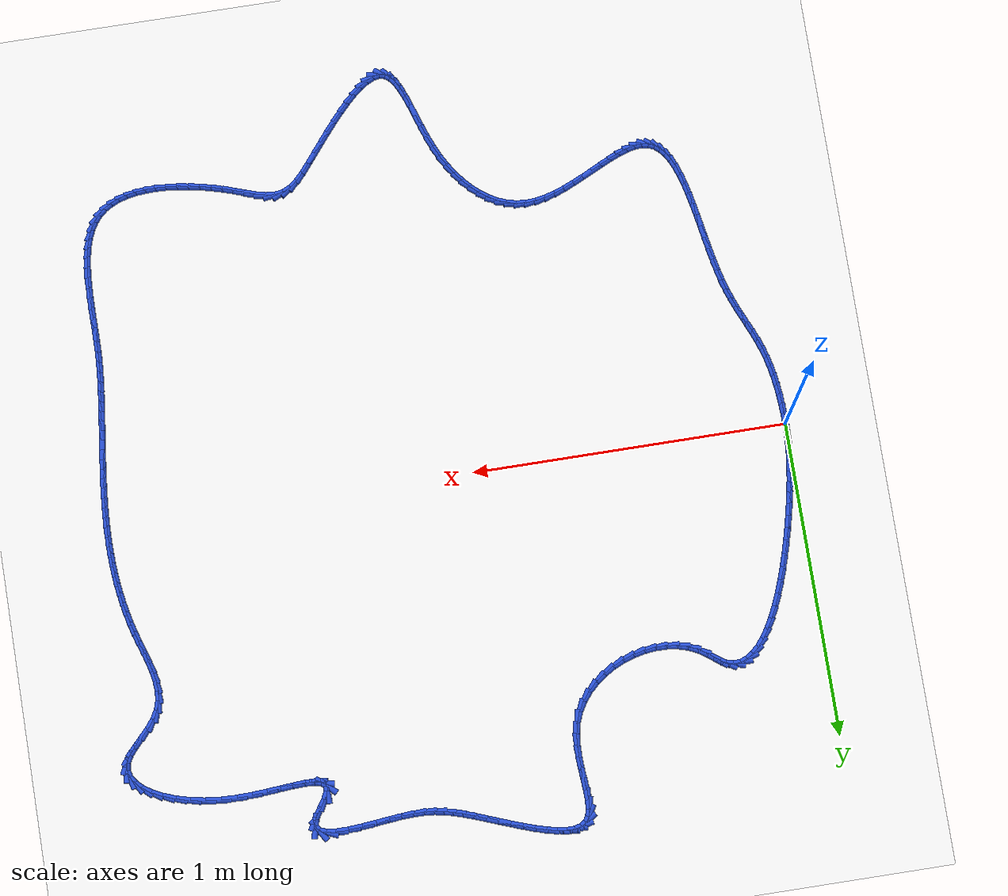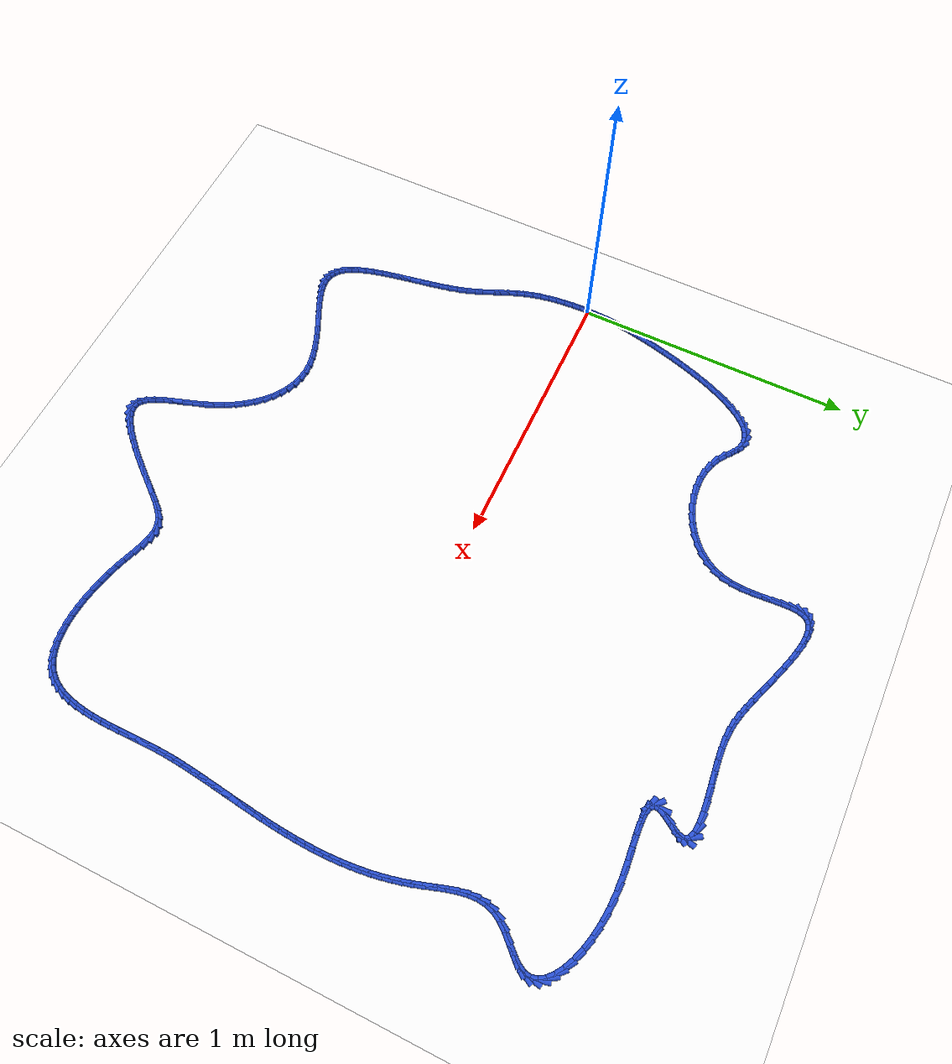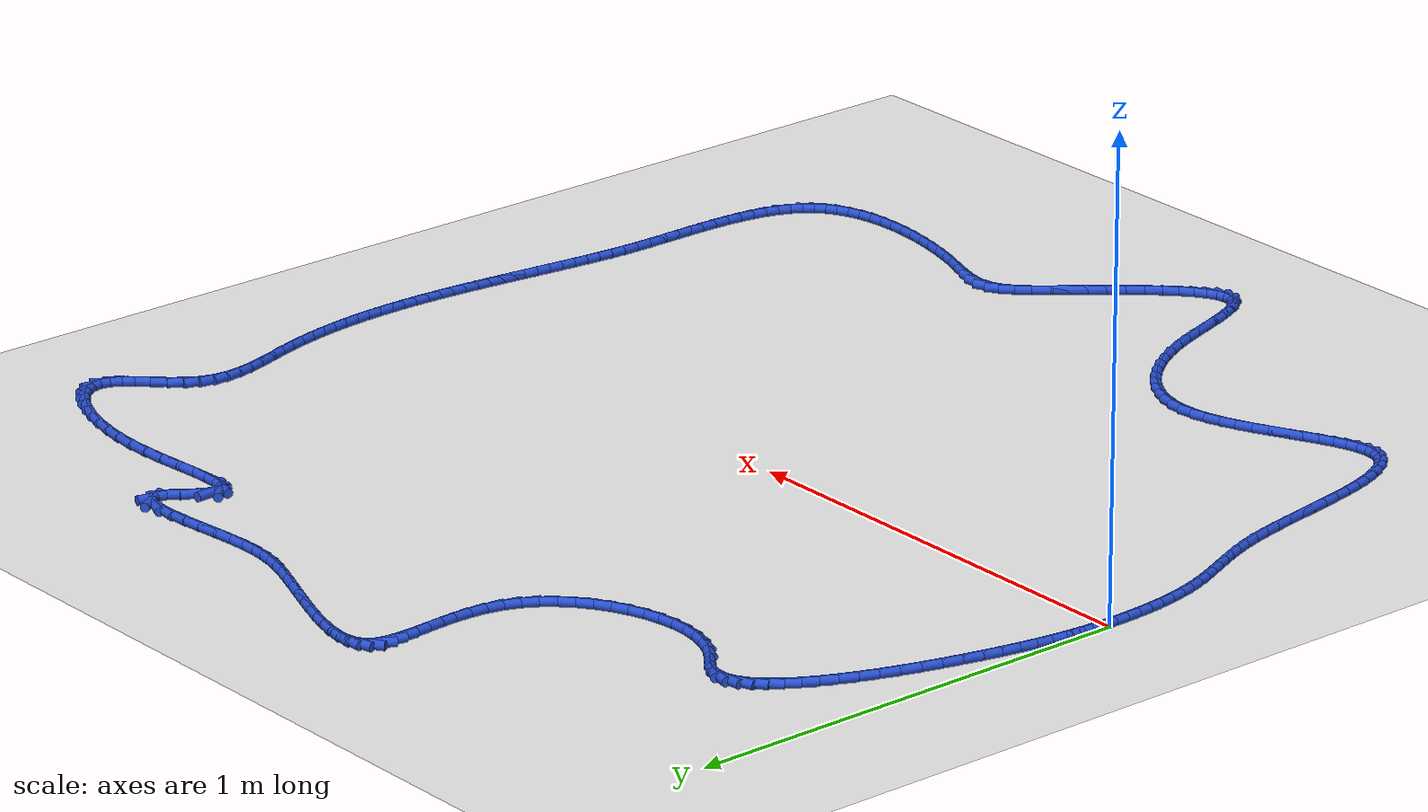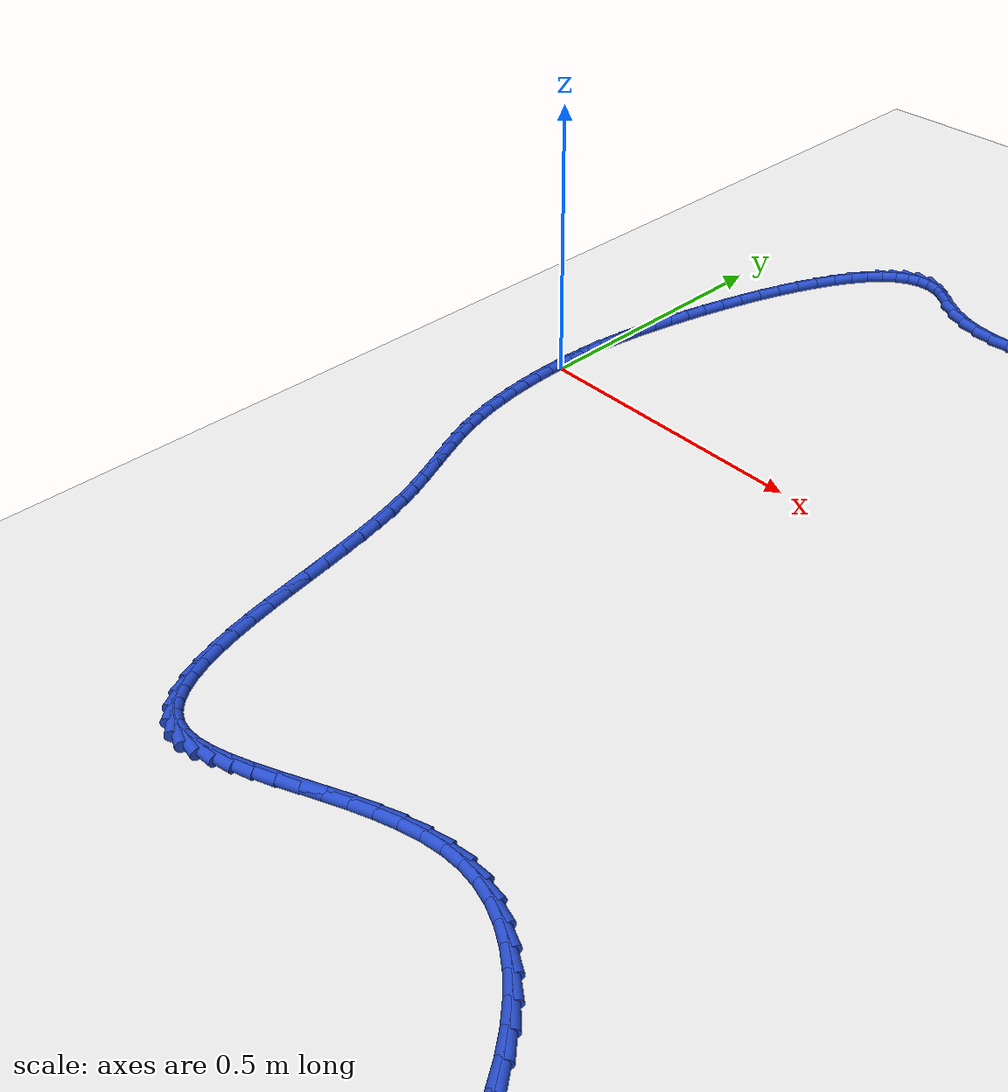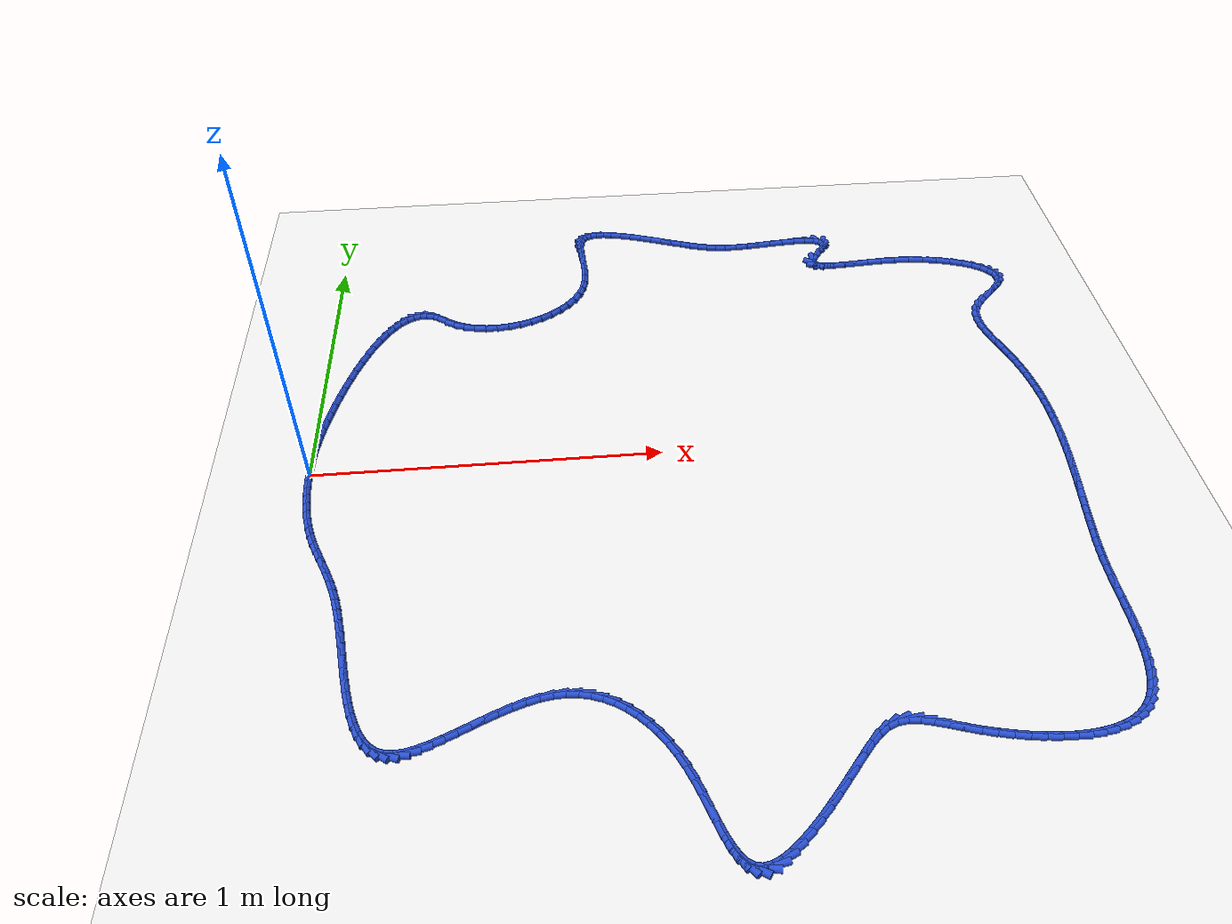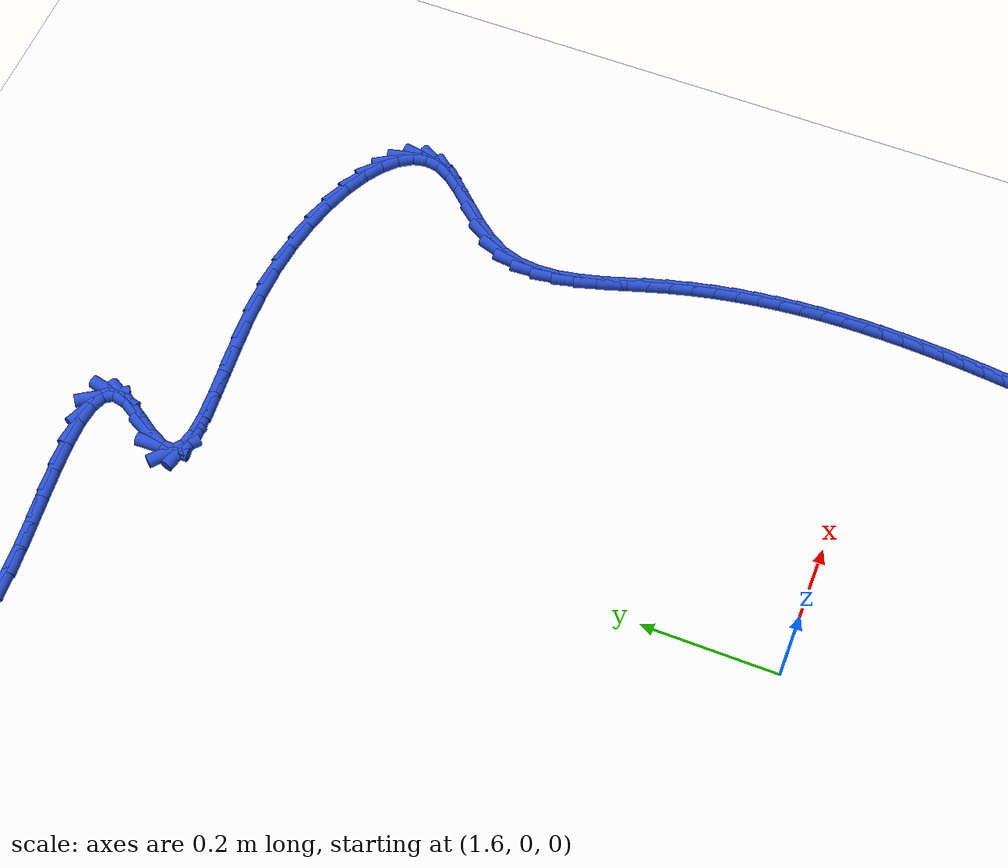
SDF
<sdf version="1.6">
 <world name="default">
  <light name="sun" type="directional">
   <pose>0 0 10 0 -0 0</pose>
   <diffuse>0.8 0.8 0.8 1</diffuse>
   <specular>0.2 0.2 0.2 1</specular>
   <attenuation>
    <range>1000</range>
    <constant>0.9</constant>
    <linear>0.01</linear>
    <quadratic>0.001</quadratic>
   </attenuation>
   <direction>-0.5 0.1 -0.9</direction>
  </light>
  <model name="ground_plane">
   <static>1</static>
   <link name="link">
    <collision name="collision">
     <geometry><plane><normal>0 0 1</normal><size>100 100</size></plane></geometry>
     <surface><friction><ode><mu>100</mu><mu2>50</mu2></ode></friction></surface>
    </collision>
    <visual name="visual">
     <cast_shadows>0</cast_shadows>
     <geometry><plane><normal>0 0 1</normal><size>100 100</size></plane></geometry>
     <material>
      <script><uri>file://media/materials/scripts/gazebo.material</uri><name>Gazebo/WhiteGlow</name></script>
     </material>
    </visual>
   </link>
  </model>
  <gravity>0 0 -9.8</gravity>
  <magnetic_field>6e-06 2.3e-05 -4.2e-05</magnetic_field>
  <atmosphere type="adiabatic"/>
  <physics name="default_physics" default="0" type="ode">
   <max_step_size>0.001</max_step_size>
   <real_time_factor>1</real_time_factor>
   <real_time_update_rate>1000</real_time_update_rate>
  </physics>
  <scene><ambient>0.4 0.4 0.4 1</ambient><background>0.7 0.7 0.7 1</background><shadows>1</shadows></scene>
  <spherical_coordinates>
   <surface_model>EARTH_WGS84</surface_model>
   <latitude_deg>0</latitude_deg>
   <longitude_deg>0</longitude_deg>
   <elevation>0</elevation>
   <heading_deg>0</heading_deg>
  </spherical_coordinates>
  <model name="line">
   <link name="link_0">
    <pose>1.5178830414797062e-17 -6.938893903907228e-18 0.01 0 1.57 1.5493245993481484</pose>
    <collision name="collision">
     <geometry><cylinder><radius>0.01</radius><length>0.08</length></cylinder></geometry>
    </collision>
    <visual name="visual">
     <material>
      <script><name>Gazebo/Blue</name><uri>file://media/materials/scripts/gazebo.material</uri></script>
     </material>
     <geometry><cylinder><radius>0.01</radius><length>0.08</length></cylinder></geometry>
    </visual>
   </link>
   <link name="link_1">
    <pose>0.0006433644896471292 0.029958726749112572 0.01 0 1.57 1.5203189165857924</pose>
    <collision name="collision">
     <geometry><cylinder><radius>0.01</radius><length>0.08</length></cylinder></geometry>
    </collision>
    <visual name="visual">
     <material>
      <script><name>Gazebo/Blue</name><uri>file://media/materials/scripts/gazebo.material</uri></script>
     </material>
     <geometry><cylinder><radius>0.01</radius><length>0.08</length></cylinder></geometry>
    </visual>
   </link>
   <link name="link_2">
    <pose>0.0021341002988583247 0.05946637129228414 0.01 0 1.57 1.49000517151812</pose>
    <collision name="collision">
     <geometry><cylinder><radius>0.01</radius><length>0.08</length></cylinder></geometry>
    </collision>
    <visual name="visual">
     <material>
      <script><name>Gazebo/Blue</name><uri>file://media/materials/scripts/gazebo.material</uri></script>
     </material>
     <geometry><cylinder><radius>0.01</radius><length>0.08</length></cylinder></geometry>
    </visual>
   </link>
   <link name="link_3">
    <pose>0.004521526725779866 0.0889526404908136 0.01 0 1.57 1.459748752166192</pose>
    <collision name="collision">
     <geometry><cylinder><radius>0.01</radius><length>0.08</length></cylinder></geometry>
    </collision>
    <visual name="visual">
     <material>
      <script><name>Gazebo/Blue</name><uri>file://media/materials/scripts/gazebo.material</uri></script>
     </material>
     <geometry><cylinder><radius>0.01</radius><length>0.08</length></cylinder></geometry>
    </visual>
   </link>
   <link name="link_4">
    <pose>0.007854963068558022 0.11884724120599993 0.01 0 1.57 1.4308644825525358</pose>
    <collision name="collision">
     <geometry><cylinder><radius>0.01</radius><length>0.08</length></cylinder></geometry>
    </collision>
    <visual name="visual">
     <material>
      <script><name>Gazebo/Blue</name><uri>file://media/materials/scripts/gazebo.material</uri></script>
     </material>
     <geometry><cylinder><radius>0.01</radius><length>0.08</length></cylinder></geometry>
    </visual>
   </link>
   <link name="link_5">
    <pose>0.012183728625339056 0.1495798802991419 0.01 0 1.57 1.4044311878890807</pose>
    <collision name="collision">
     <geometry><cylinder><radius>0.01</radius><length>0.08</length></cylinder></geometry>
    </collision>
    <visual name="visual">
     <material>
      <script><name>Gazebo/Blue</name><uri>file://media/materials/scripts/gazebo.material</uri></script>
     </material>
     <geometry><cylinder><radius>0.01</radius><length>0.08</length></cylinder></geometry>
    </visual>
   </link>
   <link name="link_6">
    <pose>0.017557142694269237 0.1815802646315386 0.01 0 1.57 1.3811792666914606</pose>
    <collision name="collision">
     <geometry><cylinder><radius>0.01</radius><length>0.08</length></cylinder></geometry>
    </collision>
    <visual name="visual">
     <material>
      <script><name>Gazebo/Blue</name><uri>file://media/materials/scripts/gazebo.material</uri></script>
     </material>
     <geometry><cylinder><radius>0.01</radius><length>0.08</length></cylinder></geometry>
    </visual>
   </link>
   <link name="link_7">
    <pose>0.02402452457349482 0.21527810106448872 0.01 0 1.57 1.3614479357479026</pose>
    <collision name="collision">
     <geometry><cylinder><radius>0.01</radius><length>0.08</length></cylinder></geometry>
    </collision>
    <visual name="visual">
     <material>
      <script><name>Gazebo/Blue</name><uri>file://media/materials/scripts/gazebo.material</uri></script>
     </material>
     <geometry><cylinder><radius>0.01</radius><length>0.08</length></cylinder></geometry>
    </visual>
   </link>
   <link name="link_8">
    <pose>0.03163474784347373 0.2510974351449298 0.01 0 1.57 1.3438799071415506</pose>
    <collision name="collision">
     <geometry><cylinder><radius>0.01</radius><length>0.08</length></cylinder></geometry>
    </collision>
    <visual name="visual">
     <material>
      <script><name>Gazebo/Blue</name><uri>file://media/materials/scripts/gazebo.material</uri></script>
     </material>
     <geometry><cylinder><radius>0.01</radius><length>0.08</length></cylinder></geometry>
    </visual>
   </link>
   <link name="link_9">
    <pose>0.04040758389248529 0.2890926688924378 0.01 0 1.57 1.3258168243298414</pose>
    <collision name="collision">
     <geometry><cylinder><radius>0.01</radius><length>0.08</length></cylinder></geometry>
    </collision>
    <visual name="visual">
     <material>
      <script><name>Gazebo/Blue</name><uri>file://media/materials/scripts/gazebo.material</uri></script>
     </material>
     <geometry><cylinder><radius>0.01</radius><length>0.08</length></cylinder></geometry>
    </visual>
   </link>
   <link name="link_10">
    <pose>0.050316284232610205 0.3287273288686516 0.01 0 1.57 1.306424946240853</pose>
    <collision name="collision">
     <geometry><cylinder><radius>0.01</radius><length>0.08</length></cylinder></geometry>
    </collision>
    <visual name="visual">
     <material>
      <script><name>Gazebo/Blue</name><uri>file://media/materials/scripts/gazebo.material</uri></script>
     </material>
     <geometry><cylinder><radius>0.01</radius><length>0.08</length></cylinder></geometry>
    </visual>
   </link>
   <link name="link_11">
    <pose>0.06132992902549046 0.36941195893615586 0.01 0 1.57 1.2850545815913803</pose>
    <collision name="collision">
     <geometry><cylinder><radius>0.01</radius><length>0.08</length></cylinder></geometry>
    </collision>
    <visual name="visual">
     <material>
      <script><name>Gazebo/Blue</name><uri>file://media/materials/scripts/gazebo.material</uri></script>
     </material>
     <geometry><cylinder><radius>0.01</radius><length>0.08</length></cylinder></geometry>
    </visual>
   </link>
   <link name="link_12">
    <pose>0.07341759843276806 0.4105571029575351 0.01 0 1.57 1.260969768004758</pose>
    <collision name="collision">
     <geometry><cylinder><radius>0.01</radius><length>0.08</length></cylinder></geometry>
    </collision>
    <visual name="visual">
     <material>
      <script><name>Gazebo/Blue</name><uri>file://media/materials/scripts/gazebo.material</uri></script>
     </material>
     <geometry><cylinder><radius>0.01</radius><length>0.08</length></cylinder></geometry>
    </visual>
   </link>
   <link name="link_13">
    <pose>0.08654837261608499 0.45157330479537383 0.01 0 1.57 1.2332656017713683</pose>
    <collision name="collision">
     <geometry><cylinder><radius>0.01</radius><length>0.08</length></cylinder></geometry>
    </collision>
    <visual name="visual">
     <material>
      <script><name>Gazebo/Blue</name><uri>file://media/materials/scripts/gazebo.material</uri></script>
     </material>
     <geometry><cylinder><radius>0.01</radius><length>0.08</length></cylinder></geometry>
    </visual>
   </link>
   <link name="link_14">
    <pose>0.10069133173708325 0.49187110831225667 0.01 0 1.57 1.2007637937305777</pose>
    <collision name="collision">
     <geometry><cylinder><radius>0.01</radius><length>0.08</length></cylinder></geometry>
    </collision>
    <visual name="visual">
     <material>
      <script><name>Gazebo/Blue</name><uri>file://media/materials/scripts/gazebo.material</uri></script>
     </material>
     <geometry><cylinder><radius>0.01</radius><length>0.08</length></cylinder></geometry>
    </visual>
   </link>
   <link name="link_15">
    <pose>0.11581555595740484 0.530861057370768 0.01 0 1.57 1.161863694016493</pose>
    <collision name="collision">
     <geometry><cylinder><radius>0.01</radius><length>0.08</length></cylinder></geometry>
    </collision>
    <visual name="visual">
     <material>
      <script><name>Gazebo/Blue</name><uri>file://media/materials/scripts/gazebo.material</uri></script>
     </material>
     <geometry><cylinder><radius>0.01</radius><length>0.08</length></cylinder></geometry>
    </visual>
   </link>
   <link name="link_16">
    <pose>0.13189012543869175 0.5679536958334926 0.01 0 1.57 1.1143161216454736</pose>
    <collision name="collision">
     <geometry><cylinder><radius>0.01</radius><length>0.08</length></cylinder></geometry>
    </collision>
    <visual name="visual">
     <material>
      <script><name>Gazebo/Blue</name><uri>file://media/materials/scripts/gazebo.material</uri></script>
     </material>
     <geometry><cylinder><radius>0.01</radius><length>0.08</length></cylinder></geometry>
    </visual>
   </link>
   <link name="link_17">
    <pose>0.14888412034258597 0.6025595675630149 0.01 0 1.57 1.0548704995543596</pose>
    <collision name="collision">
     <geometry><cylinder><radius>0.01</radius><length>0.08</length></cylinder></geometry>
    </collision>
    <visual name="visual">
     <material>
      <script><name>Gazebo/Blue</name><uri>file://media/materials/scripts/gazebo.material</uri></script>
     </material>
     <geometry><cylinder><radius>0.01</radius><length>0.08</length></cylinder></geometry>
    </visual>
   </link>
   <link name="link_18">
    <pose>0.1667666208307295 0.6340892164219193 0.01 0 1.57 0.9787274159808793</pose>
    <collision name="collision">
     <geometry><cylinder><radius>0.01</radius><length>0.08</length></cylinder></geometry>
    </collision>
    <visual name="visual">
     <material>
      <script><name>Gazebo/Blue</name><uri>file://media/materials/scripts/gazebo.material</uri></script>
     </material>
     <geometry><cylinder><radius>0.01</radius><length>0.08</length></cylinder></geometry>
    </visual>
   </link>
   <link name="link_19">
    <pose>0.18550670706476427 0.6619531862727903 0.01 0 1.57 0.8787457110928412</pose>
    <collision name="collision">
     <geometry><cylinder><radius>0.01</radius><length>0.08</length></cylinder></geometry>
    </collision>
    <visual name="visual">
     <material>
      <script><name>Gazebo/Blue</name><uri>file://media/materials/scripts/gazebo.material</uri></script>
     </material>
     <geometry><cylinder><radius>0.01</radius><length>0.08</length></cylinder></geometry>
    </visual>
   </link>
   <link name="link_20">
    <pose>0.2050734592063324 0.685562020978213 0.01 0 1.57 0.744572715721797</pose>
    <collision name="collision">
     <geometry><cylinder><radius>0.01</radius><length>0.08</length></cylinder></geometry>
    </collision>
    <visual name="visual">
     <material>
      <script><name>Gazebo/Blue</name><uri>file://media/materials/scripts/gazebo.material</uri></script>
     </material>
     <geometry><cylinder><radius>0.01</radius><length>0.08</length></cylinder></geometry>
    </visual>
   </link>
   <link name="link_21">
    <pose>0.22543595741707578 0.7043262644007712 0.01 0 1.57 0.5628635048004264</pose>
    <collision name="collision">
     <geometry><cylinder><radius>0.01</radius><length>0.08</length></cylinder></geometry>
    </collision>
    <visual name="visual">
     <material>
      <script><name>Gazebo/Blue</name><uri>file://media/materials/scripts/gazebo.material</uri></script>
     </material>
     <geometry><cylinder><radius>0.01</radius><length>0.08</length></cylinder></geometry>
    </visual>
   </link>
   <link name="link_22">
    <pose>0.24656328185863646 0.7176564604030499 0.01 0 1.57 0.3225578829213657</pose>
    <collision name="collision">
     <geometry><cylinder><radius>0.01</radius><length>0.08</length></cylinder></geometry>
    </collision>
    <visual name="visual">
     <material>
      <script><name>Gazebo/Blue</name><uri>file://media/materials/scripts/gazebo.material</uri></script>
     </material>
     <geometry><cylinder><radius>0.01</radius><length>0.08</length></cylinder></geometry>
    </visual>
   </link>
   <link name="link_23">
    <pose>0.26842451269265644 0.7249631528476334 0.01 0 1.57 0.03073513604448013</pose>
    <collision name="collision">
     <geometry><cylinder><radius>0.01</radius><length>0.08</length></cylinder></geometry>
    </collision>
    <visual name="visual">
     <material>
      <script><name>Gazebo/Blue</name><uri>file://media/materials/scripts/gazebo.material</uri></script>
     </material>
     <geometry><cylinder><radius>0.01</radius><length>0.08</length></cylinder></geometry>
    </visual>
   </link>
   <link name="link_24">
    <pose>0.29098873008077775 0.7256568855971066 0.01 0 1.57 -0.27310940792835076</pose>
    <collision name="collision">
     <geometry><cylinder><radius>0.01</radius><length>0.08</length></cylinder></geometry>
    </collision>
    <visual name="visual">
     <material>
      <script><name>Gazebo/Blue</name><uri>file://media/materials/scripts/gazebo.material</uri></script>
     </material>
     <geometry><cylinder><radius>0.01</radius><length>0.08</length></cylinder></geometry>
    </visual>
   </link>
   <link name="link_25">
    <pose>0.3142250141846421 0.7191482025140533 0.01 0 1.57 -0.5346978834300044</pose>
    <collision name="collision">
     <geometry><cylinder><radius>0.01</radius><length>0.08</length></cylinder></geometry>
    </collision>
    <visual name="visual">
     <material>
      <script><name>Gazebo/Blue</name><uri>file://media/materials/scripts/gazebo.material</uri></script>
     </material>
     <geometry><cylinder><radius>0.01</radius><length>0.08</length></cylinder></geometry>
    </visual>
   </link>
   <link name="link_26">
    <pose>0.33812722866200473 0.7049922321861407 0.01 0 1.57 -0.6514536763656009</pose>
    <collision name="collision">
     <geometry><cylinder><radius>0.01</radius><length>0.08</length></cylinder></geometry>
    </collision>
    <visual name="visual">
     <material>
      <script><name>Gazebo/Blue</name><uri>file://media/materials/scripts/gazebo.material</uri></script>
     </material>
     <geometry><cylinder><radius>0.01</radius><length>0.08</length></cylinder></geometry>
    </visual>
   </link>
   <link name="link_27">
    <pose>0.36322279691538767 0.6858568435771673 0.01 0 1.57 -0.5943265804608738</pose>
    <collision name="collision">
     <geometry><cylinder><radius>0.01</radius><length>0.08</length></cylinder></geometry>
    </collision>
    <visual name="visual">
     <material>
      <script><name>Gazebo/Blue</name><uri>file://media/materials/scripts/gazebo.material</uri></script>
     </material>
     <geometry><cylinder><radius>0.01</radius><length>0.08</length></cylinder></geometry>
    </visual>
   </link>
   <link name="link_28">
    <pose>0.3905478302028238 0.66738949042095 0.01 0 1.57 -0.4353648797650099</pose>
    <collision name="collision">
     <geometry><cylinder><radius>0.01</radius><length>0.08</length></cylinder></geometry>
    </collision>
    <visual name="visual">
     <material>
      <script><name>Gazebo/Blue</name><uri>file://media/materials/scripts/gazebo.material</uri></script>
     </material>
     <geometry><cylinder><radius>0.01</radius><length>0.08</length></cylinder></geometry>
    </visual>
   </link>
   <link name="link_29">
    <pose>0.4206173248397586 0.6534032545264427 0.01 0 1.57 -0.28005038179543834</pose>
    <collision name="collision">
     <geometry><cylinder><radius>0.01</radius><length>0.08</length></cylinder></geometry>
    </collision>
    <visual name="visual">
     <material>
      <script><name>Gazebo/Blue</name><uri>file://media/materials/scripts/gazebo.material</uri></script>
     </material>
     <geometry><cylinder><radius>0.01</radius><length>0.08</length></cylinder></geometry>
    </visual>
   </link>
   <link name="link_30">
    <pose>0.452947092596216 0.6441049264165343 0.01 0 1.57 -0.14003372184484442</pose>
    <collision name="collision">
     <geometry><cylinder><radius>0.01</radius><length>0.08</length></cylinder></geometry>
    </collision>
    <visual name="visual">
     <material>
      <script><name>Gazebo/Blue</name><uri>file://media/materials/scripts/gazebo.material</uri></script>
     </material>
     <geometry><cylinder><radius>0.01</radius><length>0.08</length></cylinder></geometry>
    </visual>
   </link>
   <link name="link_31">
    <pose>0.48694526950811706 0.6393126696448582 0.01 0 1.57 -0.013342774439727851</pose>
    <collision name="collision">
     <geometry><cylinder><radius>0.01</radius><length>0.08</length></cylinder></geometry>
    </collision>
    <visual name="visual">
     <material>
      <script><name>Gazebo/Blue</name><uri>file://media/materials/scripts/gazebo.material</uri></script>
     </material>
     <geometry><cylinder><radius>0.01</radius><length>0.08</length></cylinder></geometry>
    </visual>
   </link>
   <link name="link_32">
    <pose>0.5220199916113832 0.6388446477650479 0.01 0 1.57 0.10296523522276674</pose>
    <collision name="collision">
     <geometry><cylinder><radius>0.01</radius><length>0.08</length></cylinder></geometry>
    </collision>
    <visual name="visual">
     <material>
      <script><name>Gazebo/Blue</name><uri>file://media/materials/scripts/gazebo.material</uri></script>
     </material>
     <geometry><cylinder><radius>0.01</radius><length>0.08</length></cylinder></geometry>
    </visual>
   </link>
   <link name="link_33">
    <pose>0.5575793949419354 0.6425190243307363 0.01 0 1.57 0.2121188361501036</pose>
    <collision name="collision">
     <geometry><cylinder><radius>0.01</radius><length>0.08</length></cylinder></geometry>
    </collision>
    <visual name="visual">
     <material>
      <script><name>Gazebo/Blue</name><uri>file://media/materials/scripts/gazebo.material</uri></script>
     </material>
     <geometry><cylinder><radius>0.01</radius><length>0.08</length></cylinder></geometry>
    </visual>
   </link>
   <link name="link_34">
    <pose>0.5930316155356954 0.6501539628955569 0.01 0 1.57 0.31732275041235575</pose>
    <collision name="collision">
     <geometry><cylinder><radius>0.01</radius><length>0.08</length></cylinder></geometry>
    </collision>
    <visual name="visual">
     <material>
      <script><name>Gazebo/Blue</name><uri>file://media/materials/scripts/gazebo.material</uri></script>
     </material>
     <geometry><cylinder><radius>0.01</radius><length>0.08</length></cylinder></geometry>
    </visual>
   </link>
   <link name="link_35">
    <pose>0.6277847894285842 0.6615676270131429 0.01 0 1.57 0.4216736990604275</pose>
    <collision name="collision">
     <geometry><cylinder><radius>0.01</radius><length>0.08</length></cylinder></geometry>
    </collision>
    <visual name="visual">
     <material>
      <script><name>Gazebo/Blue</name><uri>file://media/materials/scripts/gazebo.material</uri></script>
     </material>
     <geometry><cylinder><radius>0.01</radius><length>0.08</length></cylinder></geometry>
    </visual>
   </link>
   <link name="link_36">
    <pose>0.6612470526565224 0.6765781802371275 0.01 0 1.57 0.5281745608530213</pose>
    <collision name="collision">
     <geometry><cylinder><radius>0.01</radius><length>0.08</length></cylinder></geometry>
    </collision>
    <visual name="visual">
     <material>
      <script><name>Gazebo/Blue</name><uri>file://media/materials/scripts/gazebo.material</uri></script>
     </material>
     <geometry><cylinder><radius>0.01</radius><length>0.08</length></cylinder></geometry>
    </visual>
   </link>
   <link name="link_37">
    <pose>0.6928265412554321 0.695003786121144 0.01 0 1.57 0.6397564895494025</pose>
    <collision name="collision">
     <geometry><cylinder><radius>0.01</radius><length>0.08</length></cylinder></geometry>
    </collision>
    <visual name="visual">
     <material>
      <script><name>Gazebo/Blue</name><uri>file://media/materials/scripts/gazebo.material</uri></script>
     </material>
     <geometry><cylinder><radius>0.01</radius><length>0.08</length></cylinder></geometry>
    </visual>
   </link>
   <link name="link_38">
    <pose>0.7219313912612343 0.7166626082188258 0.01 0 1.57 0.7592330316116664</pose>
    <collision name="collision">
     <geometry><cylinder><radius>0.01</radius><length>0.08</length></cylinder></geometry>
    </collision>
    <visual name="visual">
     <material>
      <script><name>Gazebo/Blue</name><uri>file://media/materials/scripts/gazebo.material</uri></script>
     </material>
     <geometry><cylinder><radius>0.01</radius><length>0.08</length></cylinder></geometry>
    </visual>
   </link>
   <link name="link_39">
    <pose>0.74796973870985 0.7413728100838058 0.01 0 1.57 0.8891038947510185</pose>
    <collision name="collision">
     <geometry><cylinder><radius>0.01</radius><length>0.08</length></cylinder></geometry>
    </collision>
    <visual name="visual">
     <material>
      <script><name>Gazebo/Blue</name><uri>file://media/materials/scripts/gazebo.material</uri></script>
     </material>
     <geometry><cylinder><radius>0.01</radius><length>0.08</length></cylinder></geometry>
    </visual>
   </link>
   <link name="link_40">
    <pose>0.7703497196372007 0.7689525552697178 0.01 0 1.57 1.0311234679835855</pose>
    <collision name="collision">
     <geometry><cylinder><radius>0.01</radius><length>0.08</length></cylinder></geometry>
    </collision>
    <visual name="visual">
     <material>
      <script><name>Gazebo/Blue</name><uri>file://media/materials/scripts/gazebo.material</uri></script>
     </material>
     <geometry><cylinder><radius>0.01</radius><length>0.08</length></cylinder></geometry>
    </visual>
   </link>
   <link name="link_41">
    <pose>0.7884794700792074 0.7992200073301946 0.01 0 1.57 1.1856080579545223</pose>
    <collision name="collision">
     <geometry><cylinder><radius>0.01</radius><length>0.08</length></cylinder></geometry>
    </collision>
    <visual name="visual">
     <material>
      <script><name>Gazebo/Blue</name><uri>file://media/materials/scripts/gazebo.material</uri></script>
     </material>
     <geometry><cylinder><radius>0.01</radius><length>0.08</length></cylinder></geometry>
    </visual>
   </link>
   <link name="link_42">
    <pose>0.8017671260717915 0.8319933298188698 0.01 0 1.57 1.3430135921492847</pose>
    <collision name="collision">
     <geometry><cylinder><radius>0.01</radius><length>0.08</length></cylinder></geometry>
    </collision>
    <visual name="visual">
     <material>
      <script><name>Gazebo/Blue</name><uri>file://media/materials/scripts/gazebo.material</uri></script>
     </material>
     <geometry><cylinder><radius>0.01</radius><length>0.08</length></cylinder></geometry>
    </visual>
   </link>
   <link name="link_43">
    <pose>0.8098789465952891 0.8669873735201795 0.01 0 1.57 1.4679632716919528</pose>
    <collision name="collision">
     <geometry><cylinder><radius>0.01</radius><length>0.08</length></cylinder></geometry>
    </collision>
    <visual name="visual">
     <material>
      <script><name>Gazebo/Blue</name><uri>file://media/materials/scripts/gazebo.material</uri></script>
     </material>
     <geometry><cylinder><radius>0.01</radius><length>0.08</length></cylinder></geometry>
    </visual>
   </link>
   <link name="link_44">
    <pose>0.8136420272085151 0.90345236860229 0.01 0 1.57 1.5554794061181378</pose>
    <collision name="collision">
     <geometry><cylinder><radius>0.01</radius><length>0.08</length></cylinder></geometry>
    </collision>
    <visual name="visual">
     <material>
      <script><name>Gazebo/Blue</name><uri>file://media/materials/scripts/gazebo.material</uri></script>
     </material>
     <geometry><cylinder><radius>0.01</radius><length>0.08</length></cylinder></geometry>
    </visual>
   </link>
   <link name="link_45">
    <pose>0.8142096496187313 0.9405079904144377 0.01 0 1.57 -1.5307117296640975</pose>
    <collision name="collision">
     <geometry><cylinder><radius>0.01</radius><length>0.08</length></cylinder></geometry>
    </collision>
    <visual name="visual">
     <material>
      <script><name>Gazebo/Blue</name><uri>file://media/materials/scripts/gazebo.material</uri></script>
     </material>
     <geometry><cylinder><radius>0.01</radius><length>0.08</length></cylinder></geometry>
    </visual>
   </link>
   <link name="link_46">
    <pose>0.8127351128144593 0.9772739073890978 0.01 0 1.57 -1.5044983936337826</pose>
    <collision name="collision">
     <geometry><cylinder><radius>0.01</radius><length>0.08</length></cylinder></geometry>
    </collision>
    <visual name="visual">
     <material>
      <script><name>Gazebo/Blue</name><uri>file://media/materials/scripts/gazebo.material</uri></script>
     </material>
     <geometry><cylinder><radius>0.01</radius><length>0.08</length></cylinder></geometry>
    </visual>
   </link>
   <link name="link_47">
    <pose>0.810371715784221 1.0128697879587452 0.01 0 1.57 -1.5083073278987087</pose>
    <collision name="collision">
     <geometry><cylinder><radius>0.01</radius><length>0.08</length></cylinder></geometry>
    </collision>
    <visual name="visual">
     <material>
      <script><name>Gazebo/Blue</name><uri>file://media/materials/scripts/gazebo.material</uri></script>
     </material>
     <geometry><cylinder><radius>0.01</radius><length>0.08</length></cylinder></geometry>
    </visual>
   </link>
   <link name="link_48">
    <pose>0.8082727575165376 1.0464153005558545 0.01 0 1.57 -1.5485486612729897</pose>
    <collision name="collision">
     <geometry><cylinder><radius>0.01</radius><length>0.08</length></cylinder></geometry>
    </collision>
    <visual name="visual">
     <material>
      <script><name>Gazebo/Blue</name><uri>file://media/materials/scripts/gazebo.material</uri></script>
     </material>
     <geometry><cylinder><radius>0.01</radius><length>0.08</length></cylinder></geometry>
    </visual>
   </link>
   <link name="link_49">
    <pose>0.8075915369999307 1.077030113612902 0.01 0 1.57 1.5004072270525526</pose>
    <collision name="collision">
     <geometry><cylinder><radius>0.01</radius><length>0.08</length></cylinder></geometry>
    </collision>
    <visual name="visual">
     <material>
      <script><name>Gazebo/Blue</name><uri>file://media/materials/scripts/gazebo.material</uri></script>
     </material>
     <geometry><cylinder><radius>0.01</radius><length>0.08</length></cylinder></geometry>
    </visual>
   </link>
   <link name="link_50">
    <pose>0.8094813532229218 1.1038338955623614 0.01 0 1.57 1.322158584535501</pose>
    <collision name="collision">
     <geometry><cylinder><radius>0.01</radius><length>0.08</length></cylinder></geometry>
    </collision>
    <visual name="visual">
     <material>
      <script><name>Gazebo/Blue</name><uri>file://media/materials/scripts/gazebo.material</uri></script>
     </material>
     <geometry><cylinder><radius>0.01</radius><length>0.08</length></cylinder></geometry>
    </visual>
   </link>
   <link name="link_51">
    <pose>0.8150955051740326 1.1259463148367086 0.01 0 1.57 1.0056260838000772</pose>
    <collision name="collision">
     <geometry><cylinder><radius>0.01</radius><length>0.08</length></cylinder></geometry>
    </collision>
    <visual name="visual">
     <material>
      <script><name>Gazebo/Blue</name><uri>file://media/materials/scripts/gazebo.material</uri></script>
     </material>
     <geometry><cylinder><radius>0.01</radius><length>0.08</length></cylinder></geometry>
    </visual>
   </link>
   <link name="link_52">
    <pose>0.825585951825242 1.142488181364428 0.01 0 1.57 0.5797126730652775</pose>
    <collision name="collision">
     <geometry><cylinder><radius>0.01</radius><length>0.08</length></cylinder></geometry>
    </collision>
    <visual name="visual">
     <material>
      <script><name>Gazebo/Blue</name><uri>file://media/materials/scripts/gazebo.material</uri></script>
     </material>
     <geometry><cylinder><radius>0.01</radius><length>0.08</length></cylinder></geometry>
    </visual>
   </link>
   <link name="link_53">
    <pose>0.8416243518515992 1.1529894499278184 0.01 0 1.57 0.23317377622062826</pose>
    <collision name="collision">
     <geometry><cylinder><radius>0.01</radius><length>0.08</length></cylinder></geometry>
    </collision>
    <visual name="visual">
     <material>
      <script><name>Gazebo/Blue</name><uri>file://media/materials/scripts/gazebo.material</uri></script>
     </material>
     <geometry><cylinder><radius>0.01</radius><length>0.08</length></cylinder></geometry>
    </visual>
   </link>
   <link name="link_54">
    <pose>0.8626931081235847 1.1579931454559542 0.01 0 1.57 0.008000935523754983</pose>
    <collision name="collision">
     <geometry><cylinder><radius>0.01</radius><length>0.08</length></cylinder></geometry>
    </collision>
    <visual name="visual">
     <material>
      <script><name>Gazebo/Blue</name><uri>file://media/materials/scripts/gazebo.material</uri></script>
     </material>
     <geometry><cylinder><radius>0.01</radius><length>0.08</length></cylinder></geometry>
    </visual>
   </link>
   <link name="link_55">
    <pose>0.888093740326428 1.158196378613145 0.01 0 1.57 -0.1335299036963079</pose>
    <collision name="collision">
     <geometry><cylinder><radius>0.01</radius><length>0.08</length></cylinder></geometry>
    </collision>
    <visual name="visual">
     <material>
      <script><name>Gazebo/Blue</name><uri>file://media/materials/scripts/gazebo.material</uri></script>
     </material>
     <geometry><cylinder><radius>0.01</radius><length>0.08</length></cylinder></geometry>
    </visual>
   </link>
   <link name="link_56">
    <pose>0.9171277681453605 1.1542962600637015 0.01 0 1.57 -0.2246865717283937</pose>
    <collision name="collision">
     <geometry><cylinder><radius>0.01</radius><length>0.08</length></cylinder></geometry>
    </collision>
    <visual name="visual">
     <material>
      <script><name>Gazebo/Blue</name><uri>file://media/materials/scripts/gazebo.material</uri></script>
     </material>
     <geometry><cylinder><radius>0.01</radius><length>0.08</length></cylinder></geometry>
    </visual>
   </link>
   <link name="link_57">
    <pose>0.9490967112656128 1.1469899004719326 0.01 0 1.57 -0.2848424513717335</pose>
    <collision name="collision">
     <geometry><cylinder><radius>0.01</radius><length>0.08</length></cylinder></geometry>
    </collision>
    <visual name="visual">
     <material>
      <script><name>Gazebo/Blue</name><uri>file://media/materials/scripts/gazebo.material</uri></script>
     </material>
     <geometry><cylinder><radius>0.01</radius><length>0.08</length></cylinder></geometry>
    </visual>
   </link>
   <link name="link_58">
    <pose>0.9833020893724163 1.1369744105021486 0.01 0 1.57 -0.32459478083452775</pose>
    <collision name="collision">
     <geometry><cylinder><radius>0.01</radius><length>0.08</length></cylinder></geometry>
    </collision>
    <visual name="visual">
     <material>
      <script><name>Gazebo/Blue</name><uri>file://media/materials/scripts/gazebo.material</uri></script>
     </material>
     <geometry><cylinder><radius>0.01</radius><length>0.08</length></cylinder></geometry>
    </visual>
   </link>
   <link name="link_59">
    <pose>1.0190454221510012 1.1249469008186597 0.01 0 1.57 -0.34972623825474436</pose>
    <collision name="collision">
     <geometry><cylinder><radius>0.01</radius><length>0.08</length></cylinder></geometry>
    </collision>
    <visual name="visual">
     <material>
      <script><name>Gazebo/Blue</name><uri>file://media/materials/scripts/gazebo.material</uri></script>
     </material>
     <geometry><cylinder><radius>0.01</radius><length>0.08</length></cylinder></geometry>
    </visual>
   </link>
   <link name="link_60">
    <pose>1.0556282292865977 1.111604482085775 0.01 0 1.57 -0.3632700847111157</pose>
    <collision name="collision">
     <geometry><cylinder><radius>0.01</radius><length>0.08</length></cylinder></geometry>
    </collision>
    <visual name="visual">
     <material>
      <script><name>Gazebo/Blue</name><uri>file://media/materials/scripts/gazebo.material</uri></script>
     </material>
     <geometry><cylinder><radius>0.01</radius><length>0.08</length></cylinder></geometry>
    </visual>
   </link>
   <link name="link_61">
    <pose>1.0923520304644376 1.0976442649678047 0.01 0 1.57 -0.36646991413991964</pose>
    <collision name="collision">
     <geometry><cylinder><radius>0.01</radius><length>0.08</length></cylinder></geometry>
    </collision>
    <visual name="visual">
     <material>
      <script><name>Gazebo/Blue</name><uri>file://media/materials/scripts/gazebo.material</uri></script>
     </material>
     <geometry><cylinder><radius>0.01</radius><length>0.08</length></cylinder></geometry>
    </visual>
   </link>
   <link name="link_62">
    <pose>1.1285183453697514 1.0837633601290586 0.01 0 1.57 -0.3590996452968195</pose>
    <collision name="collision">
     <geometry><cylinder><radius>0.01</radius><length>0.08</length></cylinder></geometry>
    </collision>
    <visual name="visual">
     <material>
      <script><name>Gazebo/Blue</name><uri>file://media/materials/scripts/gazebo.material</uri></script>
     </material>
     <geometry><cylinder><radius>0.01</radius><length>0.08</length></cylinder></geometry>
    </visual>
   </link>
   <link name="link_63">
    <pose>1.1634286936877696 1.0706588782338466 0.01 0 1.57 -0.33927787305790047</pose>
    <collision name="collision">
     <geometry><cylinder><radius>0.01</radius><length>0.08</length></cylinder></geometry>
    </collision>
    <visual name="visual">
     <material>
      <script><name>Gazebo/Blue</name><uri>file://media/materials/scripts/gazebo.material</uri></script>
     </material>
     <geometry><cylinder><radius>0.01</radius><length>0.08</length></cylinder></geometry>
    </visual>
   </link>
   <link name="link_64">
    <pose>1.196384595103723 1.0590279299464787 0.01 0 1.57 -0.3026590276931551</pose>
    <collision name="collision">
     <geometry><cylinder><radius>0.01</radius><length>0.08</length></cylinder></geometry>
    </collision>
    <visual name="visual">
     <material>
      <script><name>Gazebo/Blue</name><uri>file://media/materials/scripts/gazebo.material</uri></script>
     </material>
     <geometry><cylinder><radius>0.01</radius><length>0.08</length></cylinder></geometry>
    </visual>
   </link>
   <link name="link_65">
    <pose>1.2269009119795171 1.049499145244742 0.01 0 1.57 -0.2449448679200243</pose>
    <collision name="collision">
     <geometry><cylinder><radius>0.01</radius><length>0.08</length></cylinder></geometry>
    </collision>
    <visual name="visual">
     <material>
      <script><name>Gazebo/Blue</name><uri>file://media/materials/scripts/gazebo.material</uri></script>
     </material>
     <geometry><cylinder><radius>0.01</radius><length>0.08</length></cylinder></geometry>
    </visual>
   </link>
   <link name="link_66">
    <pose>1.2558852093692778 1.04225411163948 0.01 0 1.57 -0.1698315902846641</pose>
    <collision name="collision">
     <geometry><cylinder><radius>0.01</radius><length>0.08</length></cylinder></geometry>
    </collision>
    <visual name="visual">
     <material>
      <script><name>Gazebo/Blue</name><uri>file://media/materials/scripts/gazebo.material</uri></script>
     </material>
     <geometry><cylinder><radius>0.01</radius><length>0.08</length></cylinder></geometry>
    </visual>
   </link>
   <link name="link_67">
    <pose>1.2848038862430151 1.037295037012441 0.01 0 1.57 -0.08787684727158496</pose>
    <collision name="collision">
     <geometry><cylinder><radius>0.01</radius><length>0.08</length></cylinder></geometry>
    </collision>
    <visual name="visual">
     <material>
      <script><name>Gazebo/Blue</name><uri>file://media/materials/scripts/gazebo.material</uri></script>
     </material>
     <geometry><cylinder><radius>0.01</radius><length>0.08</length></cylinder></geometry>
    </visual>
   </link>
   <link name="link_68">
    <pose>1.3151248446331933 1.0346236467786207 0.01 0 1.57 -0.011507997036100481</pose>
    <collision name="collision">
     <geometry><cylinder><radius>0.01</radius><length>0.08</length></cylinder></geometry>
    </collision>
    <visual name="visual">
     <material>
      <script><name>Gazebo/Blue</name><uri>file://media/materials/scripts/gazebo.material</uri></script>
     </material>
     <geometry><cylinder><radius>0.01</radius><length>0.08</length></cylinder></geometry>
    </visual>
   </link>
   <link name="link_69">
    <pose>1.3483159865722767 1.034241666353014 0.01 0 1.57 0.05070032279711277</pose>
    <collision name="collision">
     <geometry><cylinder><radius>0.01</radius><length>0.08</length></cylinder></geometry>
    </collision>
    <visual name="visual">
     <material>
      <script><name>Gazebo/Blue</name><uri>file://media/materials/scripts/gazebo.material</uri></script>
     </material>
     <geometry><cylinder><radius>0.01</radius><length>0.08</length></cylinder></geometry>
    </visual>
   </link>
   <link name="link_70">
    <pose>1.3858262131399 1.0361450781488382 0.01 0 1.57 0.0898441458993424</pose>
    <collision name="collision">
     <geometry><cylinder><radius>0.01</radius><length>0.08</length></cylinder></geometry>
    </collision>
    <visual name="visual">
     <material>
      <script><name>Gazebo/Blue</name><uri>file://media/materials/scripts/gazebo.material</uri></script>
     </material>
     <geometry><cylinder><radius>0.01</radius><length>0.08</length></cylinder></geometry>
    </visual>
   </link>
   <link name="link_71">
    <pose>1.4277564119553832 1.0399224300801941 0.01 0 1.57 0.1029358978041506</pose>
    <collision name="collision">
     <geometry><cylinder><radius>0.01</radius><length>0.08</length></cylinder></geometry>
    </collision>
    <visual name="visual">
     <material>
      <script><name>Gazebo/Blue</name><uri>file://media/materials/scripts/gazebo.material</uri></script>
     </material>
     <geometry><cylinder><radius>0.01</radius><length>0.08</length></cylinder></geometry>
    </visual>
   </link>
   <link name="link_72">
    <pose>1.4719887962972413 1.0444916799703845 0.01 0 1.57 0.09508901460955961</pose>
    <collision name="collision">
     <geometry><cylinder><radius>0.01</radius><length>0.08</length></cylinder></geometry>
    </collision>
    <visual name="visual">
     <material>
      <script><name>Gazebo/Blue</name><uri>file://media/materials/scripts/gazebo.material</uri></script>
     </material>
     <geometry><cylinder><radius>0.01</radius><length>0.08</length></cylinder></geometry>
    </visual>
   </link>
   <link name="link_73">
    <pose>1.516198776328577 1.0487082797952374 0.01 0 1.57 0.06486843381105337</pose>
    <collision name="collision">
     <geometry><cylinder><radius>0.01</radius><length>0.08</length></cylinder></geometry>
    </collision>
    <visual name="visual">
     <material>
      <script><name>Gazebo/Blue</name><uri>file://media/materials/scripts/gazebo.material</uri></script>
     </material>
     <geometry><cylinder><radius>0.01</radius><length>0.08</length></cylinder></geometry>
    </visual>
   </link>
   <link name="link_74">
    <pose>1.5580617622124913 1.0514276815305805 0.01 0 1.57 0.002087996279838644</pose>
    <collision name="collision">
     <geometry><cylinder><radius>0.01</radius><length>0.08</length></cylinder></geometry>
    </collision>
    <visual name="visual">
     <material>
      <script><name>Gazebo/Blue</name><uri>file://media/materials/scripts/gazebo.material</uri></script>
     </material>
     <geometry><cylinder><radius>0.01</radius><length>0.08</length></cylinder></geometry>
    </visual>
   </link>
   <link name="link_75">
    <pose>1.5952531641120853 1.0515053371522414 0.01 0 1.57 -0.1222099374732203</pose>
    <collision name="collision">
     <geometry><cylinder><radius>0.01</radius><length>0.08</length></cylinder></geometry>
    </collision>
    <visual name="visual">
     <material>
      <script><name>Gazebo/Blue</name><uri>file://media/materials/scripts/gazebo.material</uri></script>
     </material>
     <geometry><cylinder><radius>0.01</radius><length>0.08</length></cylinder></geometry>
    </visual>
   </link>
   <link name="link_76">
    <pose>1.6254483921904608 1.047796698636049 0.01 0 1.57 -0.39241259022017205</pose>
    <collision name="collision">
     <geometry><cylinder><radius>0.01</radius><length>0.08</length></cylinder></geometry>
    </collision>
    <visual name="visual">
     <material>
      <script><name>Gazebo/Blue</name><uri>file://media/materials/scripts/gazebo.material</uri></script>
     </material>
     <geometry><cylinder><radius>0.01</radius><length>0.08</length></cylinder></geometry>
    </visual>
   </link>
   <link name="link_77">
    <pose>1.6463228566107189 1.0391572179578308 0.01 0 1.57 -1.0106192882021907</pose>
    <collision name="collision">
     <geometry><cylinder><radius>0.01</radius><length>0.08</length></cylinder></geometry>
    </collision>
    <visual name="visual">
     <material>
      <script><name>Gazebo/Blue</name><uri>file://media/materials/scripts/gazebo.material</uri></script>
     </material>
     <geometry><cylinder><radius>0.01</radius><length>0.08</length></cylinder></geometry>
    </visual>
   </link>
   <link name="link_78">
    <pose>1.6555519675359616 1.0244423470934145 0.01 0 1.57 1.3610289629077619</pose>
    <collision name="collision">
     <geometry><cylinder><radius>0.01</radius><length>0.08</length></cylinder></geometry>
    </collision>
    <visual name="visual">
     <material>
      <script><name>Gazebo/Blue</name><uri>file://media/materials/scripts/gazebo.material</uri></script>
     </material>
     <geometry><cylinder><radius>0.01</radius><length>0.08</length></cylinder></geometry>
    </visual>
   </link>
   <link name="link_79">
    <pose>1.6508912732053893 1.0025507984261726 0.01 0 1.57 1.0398791341101201</pose>
    <collision name="collision">
     <geometry><cylinder><radius>0.01</radius><length>0.08</length></cylinder></geometry>
    </collision>
    <visual name="visual">
     <material>
      <script><name>Gazebo/Blue</name><uri>file://media/materials/scripts/gazebo.material</uri></script>
     </material>
     <geometry><cylinder><radius>0.01</radius><length>0.08</length></cylinder></geometry>
    </visual>
   </link>
   <link name="link_80">
    <pose>1.6346069159807266 0.9748162085291442 0.01 0 1.57 0.9882235811372846</pose>
    <collision name="collision">
     <geometry><cylinder><radius>0.01</radius><length>0.08</length></cylinder></geometry>
    </collision>
    <visual name="visual">
     <material>
      <script><name>Gazebo/Blue</name><uri>file://media/materials/scripts/gazebo.material</uri></script>
     </material>
     <geometry><cylinder><radius>0.01</radius><length>0.08</length></cylinder></geometry>
    </visual>
   </link>
   <link name="link_81">
    <pose>1.6157904563852448 0.9462567343145302 0.01 0 1.57 1.1166185757258085</pose>
    <collision name="collision">
     <geometry><cylinder><radius>0.01</radius><length>0.08</length></cylinder></geometry>
    </collision>
    <visual name="visual">
     <material>
      <script><name>Gazebo/Blue</name><uri>file://media/materials/scripts/gazebo.material</uri></script>
     </material>
     <geometry><cylinder><radius>0.01</radius><length>0.08</length></cylinder></geometry>
    </visual>
   </link>
   <link name="link_82">
    <pose>1.6040213268180943 0.9221504398472864 0.01 0 1.57 -1.53564687889813</pose>
    <collision name="collision">
     <geometry><cylinder><radius>0.01</radius><length>0.08</length></cylinder></geometry>
    </collision>
    <visual name="visual">
     <material>
      <script><name>Gazebo/Blue</name><uri>file://media/materials/scripts/gazebo.material</uri></script>
     </material>
     <geometry><cylinder><radius>0.01</radius><length>0.08</length></cylinder></geometry>
    </visual>
   </link>
   <link name="link_83">
    <pose>1.604614223447217 0.9052895082224606 0.01 0 1.57 -0.7206442717413866</pose>
    <collision name="collision">
     <geometry><cylinder><radius>0.01</radius><length>0.08</length></cylinder></geometry>
    </collision>
    <visual name="visual">
     <material>
      <script><name>Gazebo/Blue</name><uri>file://media/materials/scripts/gazebo.material</uri></script>
     </material>
     <geometry><cylinder><radius>0.01</radius><length>0.08</length></cylinder></geometry>
    </visual>
   </link>
   <link name="link_84">
    <pose>1.616572745045639 0.8947874338512746 0.01 0 1.57 -0.2394508467682611</pose>
    <collision name="collision">
     <geometry><cylinder><radius>0.01</radius><length>0.08</length></cylinder></geometry>
    </collision>
    <visual name="visual">
     <material>
      <script><name>Gazebo/Blue</name><uri>file://media/materials/scripts/gazebo.material</uri></script>
     </material>
     <geometry><cylinder><radius>0.01</radius><length>0.08</length></cylinder></geometry>
    </visual>
   </link>
   <link name="link_85">
    <pose>1.6383911288918083 0.889460808364208 0.01 0 1.57 -0.04420304498912993</pose>
    <collision name="collision">
     <geometry><cylinder><radius>0.01</radius><length>0.08</length></cylinder></geometry>
    </collision>
    <visual name="visual">
     <material>
      <script><name>Gazebo/Blue</name><uri>file://media/materials/scripts/gazebo.material</uri></script>
     </material>
     <geometry><cylinder><radius>0.01</radius><length>0.08</length></cylinder></geometry>
    </visual>
   </link>
   <link name="link_86">
    <pose>1.6685636122641734 0.8881262233917403 0.01 0 1.57 0.03979568619891079</pose>
    <collision name="collision">
     <geometry><cylinder><radius>0.01</radius><length>0.08</length></cylinder></geometry>
    </collision>
    <visual name="visual">
     <material>
      <script><name>Gazebo/Blue</name><uri>file://media/materials/scripts/gazebo.material</uri></script>
     </material>
     <geometry><cylinder><radius>0.01</radius><length>0.08</length></cylinder></geometry>
    </visual>
   </link>
   <link name="link_87">
    <pose>1.7055844324411822 0.8896002705643514 0.01 0 1.57 0.07302906951793103</pose>
    <collision name="collision">
     <geometry><cylinder><radius>0.01</radius><length>0.08</length></cylinder></geometry>
    </collision>
    <visual name="visual">
     <material>
      <script><name>Gazebo/Blue</name><uri>file://media/materials/scripts/gazebo.material</uri></script>
     </material>
     <geometry><cylinder><radius>0.01</radius><length>0.08</length></cylinder></geometry>
    </visual>
   </link>
   <link name="link_88">
    <pose>1.7479478267012827 0.892699541512521 0.01 0 1.57 0.07649698482547174</pose>
    <collision name="collision">
     <geometry><cylinder><radius>0.01</radius><length>0.08</length></cylinder></geometry>
    </collision>
    <visual name="visual">
     <material>
      <script><name>Gazebo/Blue</name><uri>file://media/materials/scripts/gazebo.material</uri></script>
     </material>
     <geometry><cylinder><radius>0.01</radius><length>0.08</length></cylinder></geometry>
    </visual>
   </link>
   <link name="link_89">
    <pose>1.7941480323229242 0.8962406278667288 0.01 0 1.57 0.05762048660900701</pose>
    <collision name="collision">
     <geometry><cylinder><radius>0.01</radius><length>0.08</length></cylinder></geometry>
    </collision>
    <visual name="visual">
     <material>
      <script><name>Gazebo/Blue</name><uri>file://media/materials/scripts/gazebo.material</uri></script>
     </material>
     <geometry><cylinder><radius>0.01</radius><length>0.08</length></cylinder></geometry>
    </visual>
   </link>
   <link name="link_90">
    <pose>1.8426792865845527 0.899040121257454 0.01 0 1.57 0.017716002057954643</pose>
    <collision name="collision">
     <geometry><cylinder><radius>0.01</radius><length>0.08</length></cylinder></geometry>
    </collision>
    <visual name="visual">
     <material>
      <script><name>Gazebo/Blue</name><uri>file://media/materials/scripts/gazebo.material</uri></script>
     </material>
     <geometry><cylinder><radius>0.01</radius><length>0.08</length></cylinder></geometry>
    </visual>
   </link>
   <link name="link_91">
    <pose>1.8920358267646198 0.8999146133151775 0.01 0 1.57 -0.04466083925068089</pose>
    <collision name="collision">
     <geometry><cylinder><radius>0.01</radius><length>0.08</length></cylinder></geometry>
    </collision>
    <visual name="visual">
     <material>
      <script><name>Gazebo/Blue</name><uri>file://media/materials/scripts/gazebo.material</uri></script>
     </material>
     <geometry><cylinder><radius>0.01</radius><length>0.08</length></cylinder></geometry>
    </visual>
   </link>
   <link name="link_92">
    <pose>1.9407400610401226 0.8977379939901151 0.01 0 1.57 -0.11745724686859974</pose>
    <collision name="collision">
     <geometry><cylinder><radius>0.01</radius><length>0.08</length></cylinder></geometry>
    </collision>
    <visual name="visual">
     <material>
      <script><name>Gazebo/Blue</name><uri>file://media/materials/scripts/gazebo.material</uri></script>
     </material>
     <geometry><cylinder><radius>0.01</radius><length>0.08</length></cylinder></geometry>
    </visual>
   </link>
   <link name="link_93">
    <pose>1.987713128314399 0.8921951533006709 0.01 0 1.57 -0.19157112768836074</pose>
    <collision name="collision">
     <geometry><cylinder><radius>0.01</radius><length>0.08</length></cylinder></geometry>
    </collision>
    <visual name="visual">
     <material>
      <script><name>Gazebo/Blue</name><uri>file://media/materials/scripts/gazebo.material</uri></script>
     </material>
     <geometry><cylinder><radius>0.01</radius><length>0.08</length></cylinder></geometry>
    </visual>
   </link>
   <link name="link_94">
    <pose>2.032171857795337 0.8835724018263307 0.01 0 1.57 -0.2701920351205339</pose>
    <collision name="collision">
     <geometry><cylinder><radius>0.01</radius><length>0.08</length></cylinder></geometry>
    </collision>
    <visual name="visual">
     <material>
      <script><name>Gazebo/Blue</name><uri>file://media/materials/scripts/gazebo.material</uri></script>
     </material>
     <geometry><cylinder><radius>0.01</radius><length>0.08</length></cylinder></geometry>
    </visual>
   </link>
   <link name="link_95">
    <pose>2.0733400623292417 0.8721702545478441 0.01 0 1.57 -0.358013546228948</pose>
    <collision name="collision">
     <geometry><cylinder><radius>0.01</radius><length>0.08</length></cylinder></geometry>
    </collision>
    <visual name="visual">
     <material>
      <script><name>Gazebo/Blue</name><uri>file://media/materials/scripts/gazebo.material</uri></script>
     </material>
     <geometry><cylinder><radius>0.01</radius><length>0.08</length></cylinder></geometry>
    </visual>
   </link>
   <link name="link_96">
    <pose>2.1104415547624202 0.858289226445961 0.01 0 1.57 -0.4619125496463524</pose>
    <collision name="collision">
     <geometry><cylinder><radius>0.01</radius><length>0.08</length></cylinder></geometry>
    </collision>
    <visual name="visual">
     <material>
      <script><name>Gazebo/Blue</name><uri>file://media/materials/scripts/gazebo.material</uri></script>
     </material>
     <geometry><cylinder><radius>0.01</radius><length>0.08</length></cylinder></geometry>
    </visual>
   </link>
   <link name="link_97">
    <pose>2.142700147941177 0.8422298325014297 0.01 0 1.57 -0.5926032018039415</pose>
    <collision name="collision">
     <geometry><cylinder><radius>0.01</radius><length>0.08</length></cylinder></geometry>
    </collision>
    <visual name="visual">
     <material>
      <script><name>Gazebo/Blue</name><uri>file://media/materials/scripts/gazebo.material</uri></script>
     </material>
     <geometry><cylinder><radius>0.01</radius><length>0.08</length></cylinder></geometry>
    </visual>
   </link>
   <link name="link_98">
    <pose>2.1693396547118207 0.8242925876950004 0.01 0 1.57 -0.7670482542346578</pose>
    <collision name="collision">
     <geometry><cylinder><radius>0.01</radius><length>0.08</length></cylinder></geometry>
    </collision>
    <visual name="visual">
     <material>
      <script><name>Gazebo/Blue</name><uri>file://media/materials/scripts/gazebo.material</uri></script>
     </material>
     <geometry><cylinder><radius>0.01</radius><length>0.08</length></cylinder></geometry>
    </visual>
   </link>
   <link name="link_99">
    <pose>2.1895838879206537 0.8047780070074214 0.01 0 1.57 -1.009498764675532</pose>
    <collision name="collision">
     <geometry><cylinder><radius>0.01</radius><length>0.08</length></cylinder></geometry>
    </collision>
    <visual name="visual">
     <material>
      <script><name>Gazebo/Blue</name><uri>file://media/materials/scripts/gazebo.material</uri></script>
     </material>
     <geometry><cylinder><radius>0.01</radius><length>0.08</length></cylinder></geometry>
    </visual>
   </link>
   <link name="link_100">
    <pose>2.2026566604139832 0.7839866054194431 0.01 0 1.57 -1.3395615337267512</pose>
    <collision name="collision">
     <geometry><cylinder><radius>0.01</radius><length>0.08</length></cylinder></geometry>
    </collision>
    <visual name="visual">
     <material>
      <script><name>Gazebo/Blue</name><uri>file://media/materials/scripts/gazebo.material</uri></script>
     </material>
     <geometry><cylinder><radius>0.01</radius><length>0.08</length></cylinder></geometry>
    </visual>
   </link>
   <link name="link_101">
    <pose>2.2077817850381165 0.7622188979118143 0.01 0 1.57 1.4118043623769996</pose>
    <collision name="collision">
     <geometry><cylinder><radius>0.01</radius><length>0.08</length></cylinder></geometry>
    </collision>
    <visual name="visual">
     <material>
      <script><name>Gazebo/Blue</name><uri>file://media/materials/scripts/gazebo.material</uri></script>
     </material>
     <geometry><cylinder><radius>0.01</radius><length>0.08</length></cylinder></geometry>
    </visual>
   </link>
   <link name="link_102">
    <pose>2.204183074639358 0.7397753994652843 0.01 0 1.57 1.0706591382067576</pose>
    <collision name="collision">
     <geometry><cylinder><radius>0.01</radius><length>0.08</length></cylinder></geometry>
    </collision>
    <visual name="visual">
     <material>
      <script><name>Gazebo/Blue</name><uri>file://media/materials/scripts/gazebo.material</uri></script>
     </material>
     <geometry><cylinder><radius>0.01</radius><length>0.08</length></cylinder></geometry>
    </visual>
   </link>
   <link name="link_103">
    <pose>2.1916719205150774 0.7168813510437804 0.01 0 1.57 0.887145514287093</pose>
    <collision name="collision">
     <geometry><cylinder><radius>0.01</radius><length>0.08</length></cylinder></geometry>
    </collision>
    <visual name="visual">
     <material>
      <script><name>Gazebo/Blue</name><uri>file://media/materials/scripts/gazebo.material</uri></script>
     </material>
     <geometry><cylinder><radius>0.01</radius><length>0.08</length></cylinder></geometry>
    </visual>
   </link>
   <link name="link_104">
    <pose>2.1725737767305877 0.6934399198477292 0.01 0 1.57 0.8170645218951759</pose>
    <collision name="collision">
     <geometry><cylinder><radius>0.01</radius><length>0.08</length></cylinder></geometry>
    </collision>
    <visual name="visual">
     <material>
      <script><name>Gazebo/Blue</name><uri>file://media/materials/scripts/gazebo.material</uri></script>
     </material>
     <geometry><cylinder><radius>0.01</radius><length>0.08</length></cylinder></geometry>
    </visual>
   </link>
   <link name="link_105">
    <pose>2.1498863627012827 0.6692681499170171 0.01 0 1.57 0.8227248534155027</pose>
    <collision name="collision">
     <geometry><cylinder><radius>0.01</radius><length>0.08</length></cylinder></geometry>
    </collision>
    <visual name="visual">
     <material>
      <script><name>Gazebo/Blue</name><uri>file://media/materials/scripts/gazebo.material</uri></script>
     </material>
     <geometry><cylinder><radius>0.01</radius><length>0.08</length></cylinder></geometry>
    </visual>
   </link>
   <link name="link_106">
    <pose>2.126607404953584 0.6441830843805446 0.01 0 1.57 0.8977410231291956</pose>
    <collision name="collision">
     <geometry><cylinder><radius>0.01</radius><length>0.08</length></cylinder></geometry>
    </collision>
    <visual name="visual">
     <material>
      <script><name>Gazebo/Blue</name><uri>file://media/materials/scripts/gazebo.material</uri></script>
     </material>
     <geometry><cylinder><radius>0.01</radius><length>0.08</length></cylinder></geometry>
    </visual>
   </link>
   <link name="link_107">
    <pose>2.105734630013912 0.6180017663672117 0.01 0 1.57 1.0568387449022112</pose>
    <collision name="collision">
     <geometry><cylinder><radius>0.01</radius><length>0.08</length></cylinder></geometry>
    </collision>
    <visual name="visual">
     <material>
      <script><name>Gazebo/Blue</name><uri>file://media/materials/scripts/gazebo.material</uri></script>
     </material>
     <geometry><cylinder><radius>0.01</radius><length>0.08</length></cylinder></geometry>
    </visual>
   </link>
   <link name="link_108">
    <pose>2.090233043172412 0.5905442435208247 0.01 0 1.57 1.2754294400649848</pose>
    <collision name="collision">
     <geometry><cylinder><radius>0.01</radius><length>0.08</length></cylinder></geometry>
    </collision>
    <visual name="visual">
     <material>
      <script><name>Gazebo/Blue</name><uri>file://media/materials/scripts/gazebo.material</uri></script>
     </material>
     <geometry><cylinder><radius>0.01</radius><length>0.08</length></cylinder></geometry>
    </visual>
   </link>
   <link name="link_109">
    <pose>2.0814799220580156 0.5617763511132083 0.01 0 1.57 1.474329962739084</pose>
    <collision name="collision">
     <geometry><cylinder><radius>0.01</radius><length>0.08</length></cylinder></geometry>
    </collision>
    <visual name="visual">
     <material>
      <script><name>Gazebo/Blue</name><uri>file://media/materials/scripts/gazebo.material</uri></script>
     </material>
     <geometry><cylinder><radius>0.01</radius><length>0.08</length></cylinder></geometry>
    </visual>
   </link>
   <link name="link_110">
    <pose>2.0785861787759523 0.5318720256302679 0.01 0 1.57 -1.5092006525082051</pose>
    <collision name="collision">
     <geometry><cylinder><radius>0.01</radius><length>0.08</length></cylinder></geometry>
    </collision>
    <visual name="visual">
     <material>
      <script><name>Gazebo/Blue</name><uri>file://media/materials/scripts/gazebo.material</uri></script>
     </material>
     <geometry><cylinder><radius>0.01</radius><length>0.08</length></cylinder></geometry>
    </visual>
   </link>
   <link name="link_111">
    <pose>2.080488865063198 0.5010211676878509 0.01 0 1.57 -1.3943335927487148</pose>
    <collision name="collision">
     <geometry><cylinder><radius>0.01</radius><length>0.08</length></cylinder></geometry>
    </collision>
    <visual name="visual">
     <material>
      <script><name>Gazebo/Blue</name><uri>file://media/materials/scripts/gazebo.material</uri></script>
     </material>
     <geometry><cylinder><radius>0.01</radius><length>0.08</length></cylinder></geometry>
    </visual>
   </link>
   <link name="link_112">
    <pose>2.0861250326567293 0.46941367790180344 0.01 0 1.57 -1.3181349389689676</pose>
    <collision name="collision">
     <geometry><cylinder><radius>0.01</radius><length>0.08</length></cylinder></geometry>
    </collision>
    <visual name="visual">
     <material>
      <script><name>Gazebo/Blue</name><uri>file://media/materials/scripts/gazebo.material</uri></script>
     </material>
     <geometry><cylinder><radius>0.01</radius><length>0.08</length></cylinder></geometry>
    </visual>
   </link>
   <link name="link_113">
    <pose>2.0944317332935216 0.43723945688797194 0.01 0 1.57 -1.2751462137543375</pose>
    <collision name="collision">
     <geometry><cylinder><radius>0.01</radius><length>0.08</length></cylinder></geometry>
    </collision>
    <visual name="visual">
     <material>
      <script><name>Gazebo/Blue</name><uri>file://media/materials/scripts/gazebo.material</uri></script>
     </material>
     <geometry><cylinder><radius>0.01</radius><length>0.08</length></cylinder></geometry>
    </visual>
   </link>
   <link name="link_114">
    <pose>2.104346018710552 0.4046884052622029 0.01 0 1.57 -1.2615709286415946</pose>
    <collision name="collision">
     <geometry><cylinder><radius>0.01</radius><length>0.08</length></cylinder></geometry>
    </collision>
    <visual name="visual">
     <material>
      <script><name>Gazebo/Blue</name><uri>file://media/materials/scripts/gazebo.material</uri></script>
     </material>
     <geometry><cylinder><radius>0.01</radius><length>0.08</length></cylinder></geometry>
    </visual>
   </link>
   <link name="link_115">
    <pose>2.114804940644796 0.3719504236403425 0.01 0 1.57 -1.2758924909136948</pose>
    <collision name="collision">
     <geometry><cylinder><radius>0.01</radius><length>0.08</length></cylinder></geometry>
    </collision>
    <visual name="visual">
     <material>
      <script><name>Gazebo/Blue</name><uri>file://media/materials/scripts/gazebo.material</uri></script>
     </material>
     <geometry><cylinder><radius>0.01</radius><length>0.08</length></cylinder></geometry>
    </visual>
   </link>
   <link name="link_116">
    <pose>2.1247487332104575 0.3392148628233388 0.01 0 1.57 -1.3092193144514563</pose>
    <collision name="collision">
     <geometry><cylinder><radius>0.01</radius><length>0.08</length></cylinder></geometry>
    </collision>
    <visual name="visual">
     <material>
      <script><name>Gazebo/Blue</name><uri>file://media/materials/scripts/gazebo.material</uri></script>
     </material>
     <geometry><cylinder><radius>0.01</radius><length>0.08</length></cylinder></geometry>
    </visual>
   </link>
   <link name="link_117">
    <pose>2.1334777137640804 0.30660886252981917 0.01 0 1.57 -1.34375813112858</pose>
    <collision name="collision">
     <geometry><cylinder><radius>0.01</radius><length>0.08</length></cylinder></geometry>
    </collision>
    <visual name="visual">
     <material>
      <script><name>Gazebo/Blue</name><uri>file://media/materials/scripts/gazebo.material</uri></script>
     </material>
     <geometry><cylinder><radius>0.01</radius><length>0.08</length></cylinder></geometry>
    </visual>
   </link>
   <link name="link_118">
    <pose>2.1409784842028214 0.27414099405025333 0.01 0 1.57 -1.377289689485116</pose>
    <collision name="collision">
     <geometry><cylinder><radius>0.01</radius><length>0.08</length></cylinder></geometry>
    </collision>
    <visual name="visual">
     <material>
      <script><name>Gazebo/Blue</name><uri>file://media/materials/scripts/gazebo.material</uri></script>
     </material>
     <geometry><cylinder><radius>0.01</radius><length>0.08</length></cylinder></geometry>
    </visual>
   </link>
   <link name="link_119">
    <pose>2.147314704774968 0.24180651541067266 0.01 0 1.57 -1.4096474455952612</pose>
    <collision name="collision">
     <geometry><cylinder><radius>0.01</radius><length>0.08</length></cylinder></geometry>
    </collision>
    <visual name="visual">
     <material>
      <script><name>Gazebo/Blue</name><uri>file://media/materials/scripts/gazebo.material</uri></script>
     </material>
     <geometry><cylinder><radius>0.01</radius><length>0.08</length></cylinder></geometry>
    </visual>
   </link>
   <link name="link_120">
    <pose>2.152550035728809 0.20960068463710668 0.01 0 1.57 -1.4406799713433642</pose>
    <collision name="collision">
     <geometry><cylinder><radius>0.01</radius><length>0.08</length></cylinder></geometry>
    </collision>
    <visual name="visual">
     <material>
      <script><name>Gazebo/Blue</name><uri>file://media/materials/scripts/gazebo.material</uri></script>
     </material>
     <geometry><cylinder><radius>0.01</radius><length>0.08</length></cylinder></geometry>
    </visual>
   </link>
   <link name="link_121">
    <pose>2.1567481373126323 0.1775187597555856 0.01 0 1.57 -1.4702524638017678</pose>
    <collision name="collision">
     <geometry><cylinder><radius>0.01</radius><length>0.08</length></cylinder></geometry>
    </collision>
    <visual name="visual">
     <material>
      <script><name>Gazebo/Blue</name><uri>file://media/materials/scripts/gazebo.material</uri></script>
     </material>
     <geometry><cylinder><radius>0.01</radius><length>0.08</length></cylinder></geometry>
    </visual>
   </link>
   <link name="link_122">
    <pose>2.159972669774726 0.14555599879213965 0.01 0 1.57 -1.4982474482444104</pose>
    <collision name="collision">
     <geometry><cylinder><radius>0.01</radius><length>0.08</length></cylinder></geometry>
    </collision>
    <visual name="visual">
     <material>
      <script><name>Gazebo/Blue</name><uri>file://media/materials/scripts/gazebo.material</uri></script>
     </material>
     <geometry><cylinder><radius>0.01</radius><length>0.08</length></cylinder></geometry>
    </visual>
   </link>
   <link name="link_123">
    <pose>2.1622872933633794 0.11370765977279854 0.01 0 1.57 -1.5245647369995385</pose>
    <collision name="collision">
     <geometry><cylinder><radius>0.01</radius><length>0.08</length></cylinder></geometry>
    </collision>
    <visual name="visual">
     <material>
      <script><name>Gazebo/Blue</name><uri>file://media/materials/scripts/gazebo.material</uri></script>
     </material>
     <geometry><cylinder><radius>0.01</radius><length>0.08</length></cylinder></geometry>
    </visual>
   </link>
   <link name="link_124">
    <pose>2.1637556683268797 0.08196900072359342 0.01 0 1.57 -1.5491207489856658</pose>
    <collision name="collision">
     <geometry><cylinder><radius>0.01</radius><length>0.08</length></cylinder></geometry>
    </collision>
    <visual name="visual">
     <material>
      <script><name>Gazebo/Blue</name><uri>file://media/materials/scripts/gazebo.material</uri></script>
     </material>
     <geometry><cylinder><radius>0.01</radius><length>0.08</length></cylinder></geometry>
    </visual>
   </link>
   <link name="link_125">
    <pose>2.164441454913516 0.05033527967055401 0.01 0 1.57 1.5697453332981302</pose>
    <collision name="collision">
     <geometry><cylinder><radius>0.01</radius><length>0.08</length></cylinder></geometry>
    </collision>
    <visual name="visual">
     <material>
      <script><name>Gazebo/Blue</name><uri>file://media/materials/scripts/gazebo.material</uri></script>
     </material>
     <geometry><cylinder><radius>0.01</radius><length>0.08</length></cylinder></geometry>
    </visual>
   </link>
   <link name="link_126">
    <pose>2.1644083133715757 0.01880175463970998 0.01 0 1.57 1.5489025081443442</pose>
    <collision name="collision">
     <geometry><cylinder><radius>0.01</radius><length>0.08</length></cylinder></geometry>
    </collision>
    <visual name="visual">
     <material>
      <script><name>Gazebo/Blue</name><uri>file://media/materials/scripts/gazebo.material</uri></script>
     </material>
     <geometry><cylinder><radius>0.01</radius><length>0.08</length></cylinder></geometry>
    </visual>
   </link>
   <link name="link_127">
    <pose>2.163719903949348 -0.012636316342907489 0.01 0 1.57 1.5299856686447213</pose>
    <collision name="collision">
     <geometry><cylinder><radius>0.01</radius><length>0.08</length></cylinder></geometry>
    </collision>
    <visual name="visual">
     <material>
      <script><name>Gazebo/Blue</name><uri>file://media/materials/scripts/gazebo.material</uri></script>
     </material>
     <geometry><cylinder><radius>0.01</radius><length>0.08</length></cylinder></geometry>
    </visual>
   </link>
   <link name="link_128">
    <pose>2.1624398868951213 -0.043983675251268665 0.01 0 1.57 1.5130268925269656</pose>
    <collision name="collision">
     <geometry><cylinder><radius>0.01</radius><length>0.08</length></cylinder></geometry>
    </collision>
    <visual name="visual">
     <material>
      <script><name>Gazebo/Blue</name><uri>file://media/materials/scripts/gazebo.material</uri></script>
     </material>
     <geometry><cylinder><radius>0.01</radius><length>0.08</length></cylinder></geometry>
    </visual>
   </link>
   <link name="link_129">
    <pose>2.160631922457183 -0.07524506405934339 0.01 0 1.57 1.4980500087240949</pose>
    <collision name="collision">
     <geometry><cylinder><radius>0.01</radius><length>0.08</length></cylinder></geometry>
    </collision>
    <visual name="visual">
     <material>
      <script><name>Gazebo/Blue</name><uri>file://media/materials/scripts/gazebo.material</uri></script>
     </material>
     <geometry><cylinder><radius>0.01</radius><length>0.08</length></cylinder></geometry>
    </visual>
   </link>
   <link name="link_130">
    <pose>2.1583596708838217 -0.1064252247411015 0.01 0 1.57 1.4850724372768678</pose>
    <collision name="collision">
     <geometry><cylinder><radius>0.01</radius><length>0.08</length></cylinder></geometry>
    </collision>
    <visual name="visual">
     <material>
      <script><name>Gazebo/Blue</name><uri>file://media/materials/scripts/gazebo.material</uri></script>
     </material>
     <geometry><cylinder><radius>0.01</radius><length>0.08</length></cylinder></geometry>
    </visual>
   </link>
   <link name="link_131">
    <pose>2.1556867924233267 -0.13752889927051276 0.01 0 1.57 1.4741068947177456</pose>
    <collision name="collision">
     <geometry><cylinder><radius>0.01</radius><length>0.08</length></cylinder></geometry>
    </collision>
    <visual name="visual">
     <material>
      <script><name>Gazebo/Blue</name><uri>file://media/materials/scripts/gazebo.material</uri></script>
     </material>
     <geometry><cylinder><radius>0.01</radius><length>0.08</length></cylinder></geometry>
    </visual>
   </link>
   <link name="link_132">
    <pose>2.1526769473239855 -0.16856082962154695 0.01 0 1.57 1.4651629214718385</pose>
    <collision name="collision">
     <geometry><cylinder><radius>0.01</radius><length>0.08</length></cylinder></geometry>
    </collision>
    <visual name="visual">
     <material>
      <script><name>Gazebo/Blue</name><uri>file://media/materials/scripts/gazebo.material</uri></script>
     </material>
     <geometry><cylinder><radius>0.01</radius><length>0.08</length></cylinder></geometry>
    </visual>
   </link>
   <link name="link_133">
    <pose>2.149393795834086 -0.19952575776817486 0.01 0 1.57 1.4582482023728014</pose>
    <collision name="collision">
     <geometry><cylinder><radius>0.01</radius><length>0.08</length></cylinder></geometry>
    </collision>
    <visual name="visual">
     <material>
      <script><name>Gazebo/Blue</name><uri>file://media/materials/scripts/gazebo.material</uri></script>
     </material>
     <geometry><cylinder><radius>0.01</radius><length>0.08</length></cylinder></geometry>
    </visual>
   </link>
   <link name="link_134">
    <pose>2.145900998201918 -0.23042842568436447 0.01 0 1.57 1.4533696622174217</pose>
    <collision name="collision">
     <geometry><cylinder><radius>0.01</radius><length>0.08</length></cylinder></geometry>
    </collision>
    <visual name="visual">
     <material>
      <script><name>Gazebo/Blue</name><uri>file://media/materials/scripts/gazebo.material</uri></script>
     </material>
     <geometry><cylinder><radius>0.01</radius><length>0.08</length></cylinder></geometry>
    </visual>
   </link>
   <link name="link_135">
    <pose>2.142262214675768 -0.2612735753440864 0.01 0 1.57 1.4505343255031506</pose>
    <collision name="collision">
     <geometry><cylinder><radius>0.01</radius><length>0.08</length></cylinder></geometry>
    </collision>
    <visual name="visual">
     <material>
      <script><name>Gazebo/Blue</name><uri>file://media/materials/scripts/gazebo.material</uri></script>
     </material>
     <geometry><cylinder><radius>0.01</radius><length>0.08</length></cylinder></geometry>
    </visual>
   </link>
   <link name="link_136">
    <pose>2.1385411055039256 -0.29206594872131064 0.01 0 1.57 1.4497499335300346</pose>
    <collision name="collision">
     <geometry><cylinder><radius>0.01</radius><length>0.08</length></cylinder></geometry>
    </collision>
    <visual name="visual">
     <material>
      <script><name>Gazebo/Blue</name><uri>file://media/materials/scripts/gazebo.material</uri></script>
     </material>
     <geometry><cylinder><radius>0.01</radius><length>0.08</length></cylinder></geometry>
    </visual>
   </link>
   <link name="link_137">
    <pose>2.1348013309346783 -0.32281028779000676 0.01 0 1.57 1.4510253135022353</pose>
    <collision name="collision">
     <geometry><cylinder><radius>0.01</radius><length>0.08</length></cylinder></geometry>
    </collision>
    <visual name="visual">
     <material>
      <script><name>Gazebo/Blue</name><uri>file://media/materials/scripts/gazebo.material</uri></script>
     </material>
     <geometry><cylinder><radius>0.01</radius><length>0.08</length></cylinder></geometry>
    </visual>
   </link>
   <link name="link_138">
    <pose>2.131106551216315 -0.35351133452414485 0.01 0 1.57 1.454370493802974</pose>
    <collision name="collision">
     <geometry><cylinder><radius>0.01</radius><length>0.08</length></cylinder></geometry>
    </collision>
    <visual name="visual">
     <material>
      <script><name>Gazebo/Blue</name><uri>file://media/materials/scripts/gazebo.material</uri></script>
     </material>
     <geometry><cylinder><radius>0.01</radius><length>0.08</length></cylinder></geometry>
    </visual>
   </link>
   <link name="link_139">
    <pose>2.1275204265971244 -0.38417383089769447 0.01 0 1.57 1.4597965579826948</pose>
    <collision name="collision">
     <geometry><cylinder><radius>0.01</radius><length>0.08</length></cylinder></geometry>
    </collision>
    <visual name="visual">
     <material>
      <script><name>Gazebo/Blue</name><uri>file://media/materials/scripts/gazebo.material</uri></script>
     </material>
     <geometry><cylinder><radius>0.01</radius><length>0.08</length></cylinder></geometry>
    </visual>
   </link>
   <link name="link_140">
    <pose>2.124106617325393 -0.4148025188846264 0.01 0 1.57 1.4673152279584873</pose>
    <collision name="collision">
     <geometry><cylinder><radius>0.01</radius><length>0.08</length></cylinder></geometry>
    </collision>
    <visual name="visual">
     <material>
      <script><name>Gazebo/Blue</name><uri>file://media/materials/scripts/gazebo.material</uri></script>
     </material>
     <geometry><cylinder><radius>0.01</radius><length>0.08</length></cylinder></geometry>
    </visual>
   </link>
   <link name="link_141">
    <pose>2.1209287836494113 -0.4454021404589088 0.01 0 1.57 1.4775451111706688</pose>
    <collision name="collision">
     <geometry><cylinder><radius>0.01</radius><length>0.08</length></cylinder></geometry>
    </collision>
    <visual name="visual">
     <material>
      <script><name>Gazebo/Blue</name><uri>file://media/materials/scripts/gazebo.material</uri></script>
     </material>
     <geometry><cylinder><radius>0.01</radius><length>0.08</length></cylinder></geometry>
    </visual>
   </link>
   <link name="link_142">
    <pose>2.1180642294765293 -0.47603172689193485 0.01 0 1.57 1.4929434305678746</pose>
    <collision name="collision">
     <geometry><cylinder><radius>0.01</radius><length>0.08</length></cylinder></geometry>
    </collision>
    <visual name="visual">
     <material>
      <script><name>Gazebo/Blue</name><uri>file://media/materials/scripts/gazebo.material</uri></script>
     </material>
     <geometry><cylinder><radius>0.01</radius><length>0.08</length></cylinder></geometry>
    </visual>
   </link>
   <link name="link_143">
    <pose>2.1156494742302128 -0.5069859331064467 0.01 0 1.57 1.5135729845963795</pose>
    <collision name="collision">
     <geometry><cylinder><radius>0.01</radius><length>0.08</length></cylinder></geometry>
    </collision>
    <visual name="visual">
     <material>
      <script><name>Gazebo/Blue</name><uri>file://media/materials/scripts/gazebo.material</uri></script>
     </material>
     <geometry><cylinder><radius>0.01</radius><length>0.08</length></cylinder></geometry>
    </visual>
   </link>
   <link name="link_144">
    <pose>2.1138370984244363 -0.5386233224910628 0.01 0 1.57 1.5383429088464917</pose>
    <collision name="collision">
     <geometry><cylinder><radius>0.01</radius><length>0.08</length></cylinder></geometry>
    </collision>
    <visual name="visual">
     <material>
      <script><name>Gazebo/Blue</name><uri>file://media/materials/scripts/gazebo.material</uri></script>
     </material>
     <geometry><cylinder><radius>0.01</radius><length>0.08</length></cylinder></geometry>
    </visual>
   </link>
   <link name="link_145">
    <pose>2.112776342893706 -0.5712973262509051 0.01 0 1.57 1.5610616193120659</pose>
    <collision name="collision">
     <geometry><cylinder><radius>0.01</radius><length>0.08</length></cylinder></geometry>
    </collision>
    <visual name="visual">
     <material>
      <script><name>Gazebo/Blue</name><uri>file://media/materials/scripts/gazebo.material</uri></script>
     </material>
     <geometry><cylinder><radius>0.01</radius><length>0.08</length></cylinder></geometry>
    </visual>
   </link>
   <link name="link_146">
    <pose>2.1124472602907765 -0.6051013422755238 0.01 0 1.57 -1.5668445929984436</pose>
    <collision name="collision">
     <geometry><cylinder><radius>0.01</radius><length>0.08</length></cylinder></geometry>
    </collision>
    <visual name="visual">
     <material>
      <script><name>Gazebo/Blue</name><uri>file://media/materials/scripts/gazebo.material</uri></script>
     </material>
     <geometry><cylinder><radius>0.01</radius><length>0.08</length></cylinder></geometry>
    </visual>
   </link>
   <link name="link_147">
    <pose>2.1125841876876232 -0.6397511165612001 0.01 0 1.57 -1.5617589556294307</pose>
    <collision name="collision">
     <geometry><cylinder><radius>0.01</radius><length>0.08</length></cylinder></geometry>
    </collision>
    <visual name="visual">
     <material>
      <script><name>Gazebo/Blue</name><uri>file://media/materials/scripts/gazebo.material</uri></script>
     </material>
     <geometry><cylinder><radius>0.01</radius><length>0.08</length></cylinder></geometry>
    </visual>
   </link>
   <link name="link_148">
    <pose>2.1129021454287455 -0.6749327063124769 0.01 0 1.57 -1.5647508727656123</pose>
    <collision name="collision">
     <geometry><cylinder><radius>0.01</radius><length>0.08</length></cylinder></geometry>
    </collision>
    <visual name="visual">
     <material>
      <script><name>Gazebo/Blue</name><uri>file://media/materials/scripts/gazebo.material</uri></script>
     </material>
     <geometry><cylinder><radius>0.01</radius><length>0.08</length></cylinder></geometry>
    </visual>
   </link>
   <link name="link_149">
    <pose>2.1131161538586407 -0.7103321687338994 0.01 0 1.57 1.5658415874892735</pose>
    <collision name="collision">
     <geometry><cylinder><radius>0.01</radius><length>0.08</length></cylinder></geometry>
    </collision>
    <visual name="visual">
     <material>
      <script><name>Gazebo/Blue</name><uri>file://media/materials/scripts/gazebo.material</uri></script>
     </material>
     <geometry><cylinder><radius>0.01</radius><length>0.08</length></cylinder></geometry>
    </visual>
   </link>
   <link name="link_150">
    <pose>2.1129412333218065 -0.7456355610300089 0.01 0 1.57 1.546474756460688</pose>
    <collision name="collision">
     <geometry><cylinder><radius>0.01</radius><length>0.08</length></cylinder></geometry>
    </collision>
    <visual name="visual">
     <material>
      <script><name>Gazebo/Blue</name><uri>file://media/materials/scripts/gazebo.material</uri></script>
     </material>
     <geometry><cylinder><radius>0.01</radius><length>0.08</length></cylinder></geometry>
    </visual>
   </link>
   <link name="link_151">
    <pose>2.1120924041627407 -0.7805289404053501 0.01 0 1.57 1.517941068026042</pose>
    <collision name="collision">
     <geometry><cylinder><radius>0.01</radius><length>0.08</length></cylinder></geometry>
    </collision>
    <visual name="visual">
     <material>
      <script><name>Gazebo/Blue</name><uri>file://media/materials/scripts/gazebo.material</uri></script>
     </material>
     <geometry><cylinder><radius>0.01</radius><length>0.08</length></cylinder></geometry>
    </visual>
   </link>
   <link name="link_152">
    <pose>2.1102846867259415 -0.8146983640644665 0.01 0 1.57 1.478950274529012</pose>
    <collision name="collision">
     <geometry><cylinder><radius>0.01</radius><length>0.08</length></cylinder></geometry>
    </collision>
    <visual name="visual">
     <material>
      <script><name>Gazebo/Blue</name><uri>file://media/materials/scripts/gazebo.material</uri></script>
     </material>
     <geometry><cylinder><radius>0.01</radius><length>0.08</length></cylinder></geometry>
    </visual>
   </link>
   <link name="link_153">
    <pose>2.107233101355908 -0.8478298892119022 0.01 0 1.57 1.4276512588641737</pose>
    <collision name="collision">
     <geometry><cylinder><radius>0.01</radius><length>0.08</length></cylinder></geometry>
    </collision>
    <visual name="visual">
     <material>
      <script><name>Gazebo/Blue</name><uri>file://media/materials/scripts/gazebo.material</uri></script>
     </material>
     <geometry><cylinder><radius>0.01</radius><length>0.08</length></cylinder></geometry>
    </visual>
   </link>
   <link name="link_154">
    <pose>2.102652668397136 -0.8796095730522001 0.01 0 1.57 1.3615680062993154</pose>
    <collision name="collision">
     <geometry><cylinder><radius>0.01</radius><length>0.08</length></cylinder></geometry>
    </collision>
    <visual name="visual">
     <material>
      <script><name>Gazebo/Blue</name><uri>file://media/materials/scripts/gazebo.material</uri></script>
     </material>
     <geometry><cylinder><radius>0.01</radius><length>0.08</length></cylinder></geometry>
    </visual>
   </link>
   <link name="link_155">
    <pose>2.096258408194124 -0.909723472789904 0.01 0 1.57 1.2776181634800723</pose>
    <collision name="collision">
     <geometry><cylinder><radius>0.01</radius><length>0.08</length></cylinder></geometry>
    </collision>
    <visual name="visual">
     <material>
      <script><name>Gazebo/Blue</name><uri>file://media/materials/scripts/gazebo.material</uri></script>
     </material>
     <geometry><cylinder><radius>0.01</radius><length>0.08</length></cylinder></geometry>
    </visual>
   </link>
   <link name="link_156">
    <pose>2.08776534109137 -0.9378576456295582 0.01 0 1.57 1.1723842745373065</pose>
    <collision name="collision">
     <geometry><cylinder><radius>0.01</radius><length>0.08</length></cylinder></geometry>
    </collision>
    <visual name="visual">
     <material>
      <script><name>Gazebo/Blue</name><uri>file://media/materials/scripts/gazebo.material</uri></script>
     </material>
     <geometry><cylinder><radius>0.01</radius><length>0.08</length></cylinder></geometry>
    </visual>
   </link>
   <link name="link_157">
    <pose>2.076888487433372 -0.9636981487757048 0.01 0 1.57 1.0429434872162242</pose>
    <collision name="collision">
     <geometry><cylinder><radius>0.01</radius><length>0.08</length></cylinder></geometry>
    </collision>
    <visual name="visual">
     <material>
      <script><name>Gazebo/Blue</name><uri>file://media/materials/scripts/gazebo.material</uri></script>
     </material>
     <geometry><cylinder><radius>0.01</radius><length>0.08</length></cylinder></geometry>
    </visual>
   </link>
   <link name="link_158">
    <pose>2.0633428675646277 -0.9869310394328884 0.01 0 1.57 0.8885863723857401</pose>
    <collision name="collision">
     <geometry><cylinder><radius>0.01</radius><length>0.08</length></cylinder></geometry>
    </collision>
    <visual name="visual">
     <material>
      <script><name>Gazebo/Blue</name><uri>file://media/materials/scripts/gazebo.material</uri></script>
     </material>
     <geometry><cylinder><radius>0.01</radius><length>0.08</length></cylinder></geometry>
    </visual>
   </link>
   <link name="link_159">
    <pose>2.0468435018296347 -1.007242374805652 0.01 0 1.57 0.7158832035427021</pose>
    <collision name="collision">
     <geometry><cylinder><radius>0.01</radius><length>0.08</length></cylinder></geometry>
    </collision>
    <visual name="visual">
     <material>
      <script><name>Gazebo/Blue</name><uri>file://media/materials/scripts/gazebo.material</uri></script>
     </material>
     <geometry><cylinder><radius>0.01</radius><length>0.08</length></cylinder></geometry>
    </visual>
   </link>
   <link name="link_160">
    <pose>2.0271608304048225 -1.0243625676851322 0.01 0 1.57 0.5512406583729766</pose>
    <collision name="collision">
     <geometry><cylinder><radius>0.01</radius><length>0.08</length></cylinder></geometry>
    </collision>
    <visual name="visual">
     <material>
      <script><name>Gazebo/Blue</name><uri>file://media/materials/scripts/gazebo.material</uri></script>
     </material>
     <geometry><cylinder><radius>0.01</radius><length>0.08</length></cylinder></geometry>
    </visual>
   </link>
   <link name="link_161">
    <pose>2.00444686297409 -1.0383274222492653 0.01 0 1.57 0.4073539535871365</pose>
    <collision name="collision">
     <geometry><cylinder><radius>0.01</radius><length>0.08</length></cylinder></geometry>
    </collision>
    <visual name="visual">
     <material>
      <script><name>Gazebo/Blue</name><uri>file://media/materials/scripts/gazebo.material</uri></script>
     </material>
     <geometry><cylinder><radius>0.01</radius><length>0.08</length></cylinder></geometry>
    </visual>
   </link>
   <link name="link_162">
    <pose>1.979014250299011 -1.0493013127019648 0.01 0 1.57 0.28473135675628813</pose>
    <collision name="collision">
     <geometry><cylinder><radius>0.01</radius><length>0.08</length></cylinder></geometry>
    </collision>
    <visual name="visual">
     <material>
      <script><name>Gazebo/Blue</name><uri>file://media/materials/scripts/gazebo.material</uri></script>
     </material>
     <geometry><cylinder><radius>0.01</radius><length>0.08</length></cylinder></geometry>
    </visual>
   </link>
   <link name="link_163">
    <pose>1.9511762032568567 -1.0574490615390209 0.01 0 1.57 0.18129434952298823</pose>
    <collision name="collision">
     <geometry><cylinder><radius>0.01</radius><length>0.08</length></cylinder></geometry>
    </collision>
    <visual name="visual">
     <material>
      <script><name>Gazebo/Blue</name><uri>file://media/materials/scripts/gazebo.material</uri></script>
     </material>
     <geometry><cylinder><radius>0.01</radius><length>0.08</length></cylinder></geometry>
    </visual>
   </link>
   <link name="link_164">
    <pose>1.9212459327248992 -1.0629354912562228 0.01 0 1.57 0.0940140746038788</pose>
    <collision name="collision">
     <geometry><cylinder><radius>0.01</radius><length>0.08</length></cylinder></geometry>
    </collision>
    <visual name="visual">
     <material>
      <script><name>Gazebo/Blue</name><uri>file://media/materials/scripts/gazebo.material</uri></script>
     </material>
     <geometry><cylinder><radius>0.01</radius><length>0.08</length></cylinder></geometry>
    </visual>
   </link>
   <link name="link_165">
    <pose>1.8895366495804098 -1.0659254243493597 0.01 0 1.57 0.019839364430289108</pose>
    <collision name="collision">
     <geometry><cylinder><radius>0.01</radius><length>0.08</length></cylinder></geometry>
    </collision>
    <visual name="visual">
     <material>
      <script><name>Gazebo/Blue</name><uri>file://media/materials/scripts/gazebo.material</uri></script>
     </material>
     <geometry><cylinder><radius>0.01</radius><length>0.08</length></cylinder></geometry>
    </visual>
   </link>
   <link name="link_166">
    <pose>1.8563615647006615 -1.0665836833142208 0.01 0 1.57 -0.04391857488852035</pose>
    <collision name="collision">
     <geometry><cylinder><radius>0.01</radius><length>0.08</length></cylinder></geometry>
    </collision>
    <visual name="visual">
     <material>
      <script><name>Gazebo/Blue</name><uri>file://media/materials/scripts/gazebo.material</uri></script>
     </material>
     <geometry><cylinder><radius>0.01</radius><length>0.08</length></cylinder></geometry>
    </visual>
   </link>
   <link name="link_167">
    <pose>1.8220338889629257 -1.065075090646596 0.01 0 1.57 -0.09949736617803581</pose>
    <collision name="collision">
     <geometry><cylinder><radius>0.01</radius><length>0.08</length></cylinder></geometry>
    </collision>
    <visual name="visual">
     <material>
      <script><name>Gazebo/Blue</name><uri>file://media/materials/scripts/gazebo.material</uri></script>
     </material>
     <geometry><cylinder><radius>0.01</radius><length>0.08</length></cylinder></geometry>
    </visual>
   </link>
   <link name="link_168">
    <pose>1.786866833244475 -1.0615644688422745 0.01 0 1.57 -0.14872128859628608</pose>
    <collision name="collision">
     <geometry><cylinder><radius>0.01</radius><length>0.08</length></cylinder></geometry>
    </collision>
    <visual name="visual">
     <material>
      <script><name>Gazebo/Blue</name><uri>file://media/materials/scripts/gazebo.material</uri></script>
     </material>
     <geometry><cylinder><radius>0.01</radius><length>0.08</length></cylinder></geometry>
    </visual>
   </link>
   <link name="link_169">
    <pose>1.75117360842258 -1.0562166403970457 0.01 0 1.57 -0.19307977196396972</pose>
    <collision name="collision">
     <geometry><cylinder><radius>0.01</radius><length>0.08</length></cylinder></geometry>
    </collision>
    <visual name="visual">
     <material>
      <script><name>Gazebo/Blue</name><uri>file://media/materials/scripts/gazebo.material</uri></script>
     </material>
     <geometry><cylinder><radius>0.01</radius><length>0.08</length></cylinder></geometry>
    </visual>
   </link>
   <link name="link_170">
    <pose>1.7152674253745133 -1.0491964278066983 0.01 0 1.57 -0.2338106481693453</pose>
    <collision name="collision">
     <geometry><cylinder><radius>0.01</radius><length>0.08</length></cylinder></geometry>
    </collision>
    <visual name="visual">
     <material>
      <script><name>Gazebo/Blue</name><uri>file://media/materials/scripts/gazebo.material</uri></script>
     </material>
     <geometry><cylinder><radius>0.01</radius><length>0.08</length></cylinder></geometry>
    </visual>
   </link>
   <link name="link_171">
    <pose>1.6794614949775473 -1.0406686535670229 0.01 0 1.57 -0.2719767002915267</pose>
    <collision name="collision">
     <geometry><cylinder><radius>0.01</radius><length>0.08</length></cylinder></geometry>
    </collision>
    <visual name="visual">
     <material>
      <script><name>Gazebo/Blue</name><uri>file://media/materials/scripts/gazebo.material</uri></script>
     </material>
     <geometry><cylinder><radius>0.01</radius><length>0.08</length></cylinder></geometry>
    </visual>
   </link>
   <link name="link_172">
    <pose>1.6440690281089516 -1.0307981401738076 0.01 0 1.57 -0.3085235119712661</pose>
    <collision name="collision">
     <geometry><cylinder><radius>0.01</radius><length>0.08</length></cylinder></geometry>
    </collision>
    <visual name="visual">
     <material>
      <script><name>Gazebo/Blue</name><uri>file://media/materials/scripts/gazebo.material</uri></script>
     </material>
     <geometry><cylinder><radius>0.01</radius><length>0.08</length></cylinder></geometry>
    </visual>
   </link>
   <link name="link_173">
    <pose>1.6094032212393148 -1.0197501376978135 0.01 0 1.57 -0.33376533481258314</pose>
    <collision name="collision">
     <geometry><cylinder><radius>0.01</radius><length>0.08</length></cylinder></geometry>
    </collision>
    <visual name="visual">
     <material>
      <script><name>Gazebo/Blue</name><uri>file://media/materials/scripts/gazebo.material</uri></script>
     </material>
     <geometry><cylinder><radius>0.01</radius><length>0.08</length></cylinder></geometry>
    </visual>
   </link>
   <link name="link_174">
    <pose>1.575763920050237 -1.0080861333035158 0.01 0 1.57 -0.3163152477539752</pose>
    <collision name="collision">
     <geometry><cylinder><radius>0.01</radius><length>0.08</length></cylinder></geometry>
    </collision>
    <visual name="visual">
     <material>
      <script><name>Gazebo/Blue</name><uri>file://media/materials/scripts/gazebo.material</uri></script>
     </material>
     <geometry><cylinder><radius>0.01</radius><length>0.08</length></cylinder></geometry>
    </visual>
   </link>
   <link name="link_175">
    <pose>1.543412900458766 -0.9974974839239825 0.01 0 1.57 -0.24253140029561432</pose>
    <collision name="collision">
     <geometry><cylinder><radius>0.01</radius><length>0.08</length></cylinder></geometry>
    </collision>
    <visual name="visual">
     <material>
      <script><name>Gazebo/Blue</name><uri>file://media/materials/scripts/gazebo.material</uri></script>
     </material>
     <geometry><cylinder><radius>0.01</radius><length>0.08</length></cylinder></geometry>
    </visual>
   </link>
   <link name="link_176">
    <pose>1.5126051972516479 -0.989875616007517 0.01 0 1.57 -0.09498124161941808</pose>
    <collision name="collision">
     <geometry><cylinder><radius>0.01</radius><length>0.08</length></cylinder></geometry>
    </collision>
    <visual name="visual">
     <material>
      <script><name>Gazebo/Blue</name><uri>file://media/materials/scripts/gazebo.material</uri></script>
     </material>
     <geometry><cylinder><radius>0.01</radius><length>0.08</length></cylinder></geometry>
    </visual>
   </link>
   <link name="link_177">
    <pose>1.4835958452156273 -0.987111956002423 0.01 0 1.57 0.14674158364329487</pose>
    <collision name="collision">
     <geometry><cylinder><radius>0.01</radius><length>0.08</length></cylinder></geometry>
    </collision>
    <visual name="visual">
     <material>
      <script><name>Gazebo/Blue</name><uri>file://media/materials/scripts/gazebo.material</uri></script>
     </material>
     <geometry><cylinder><radius>0.01</radius><length>0.08</length></cylinder></geometry>
    </visual>
   </link>
   <link name="link_178">
    <pose>1.4566393681363503 -0.9910962311982393 0.01 0 1.57 0.44208604405584384</pose>
    <collision name="collision">
     <geometry><cylinder><radius>0.01</radius><length>0.08</length></cylinder></geometry>
    </collision>
    <visual name="visual">
     <material>
      <script><name>Gazebo/Blue</name><uri>file://media/materials/scripts/gazebo.material</uri></script>
     </material>
     <geometry><cylinder><radius>0.01</radius><length>0.08</length></cylinder></geometry>
    </visual>
   </link>
   <link name="link_179">
    <pose>1.4317389386279022 -1.0028823868339072 0.01 0 1.57 0.6659064863147269</pose>
    <collision name="collision">
     <geometry><cylinder><radius>0.01</radius><length>0.08</length></cylinder></geometry>
    </collision>
    <visual name="visual">
     <material>
      <script><name>Gazebo/Blue</name><uri>file://media/materials/scripts/gazebo.material</uri></script>
     </material>
     <geometry><cylinder><radius>0.01</radius><length>0.08</length></cylinder></geometry>
    </visual>
   </link>
   <link name="link_180">
    <pose>1.4082414933263832 -1.0213422806412638 0.01 0 1.57 0.8026097560147912</pose>
    <collision name="collision">
     <geometry><cylinder><radius>0.01</radius><length>0.08</length></cylinder></geometry>
    </collision>
    <visual name="visual">
     <material>
      <script><name>Gazebo/Blue</name><uri>file://media/materials/scripts/gazebo.material</uri></script>
     </material>
     <geometry><cylinder><radius>0.01</radius><length>0.08</length></cylinder></geometry>
    </visual>
   </link>
   <link name="link_181">
    <pose>1.3853882097395411 -1.0449961046701723 0.01 0 1.57 0.8725893538672518</pose>
    <collision name="collision">
     <geometry><cylinder><radius>0.01</radius><length>0.08</length></cylinder></geometry>
    </collision>
    <visual name="visual">
     <material>
      <script><name>Gazebo/Blue</name><uri>file://media/materials/scripts/gazebo.material</uri></script>
     </material>
     <geometry><cylinder><radius>0.01</radius><length>0.08</length></cylinder></geometry>
    </visual>
   </link>
   <link name="link_182">
    <pose>1.362420265375127 -1.0723640509704946 0.01 0 1.57 0.8939527697552536</pose>
    <collision name="collision">
     <geometry><cylinder><radius>0.01</radius><length>0.08</length></cylinder></geometry>
    </collision>
    <visual name="visual">
     <material>
      <script><name>Gazebo/Blue</name><uri>file://media/materials/scripts/gazebo.material</uri></script>
     </material>
     <geometry><cylinder><radius>0.01</radius><length>0.08</length></cylinder></geometry>
    </visual>
   </link>
   <link name="link_183">
    <pose>1.338617274147672 -1.1019898766692235 0.01 0 1.57 0.8928186786376509</pose>
    <collision name="collision">
     <geometry><cylinder><radius>0.01</radius><length>0.08</length></cylinder></geometry>
    </collision>
    <visual name="visual">
     <material>
      <script><name>Gazebo/Blue</name><uri>file://media/materials/scripts/gazebo.material</uri></script>
     </material>
     <geometry><cylinder><radius>0.01</radius><length>0.08</length></cylinder></geometry>
    </visual>
   </link>
   <link name="link_184">
    <pose>1.3138309182506192 -1.1327680697301852 0.01 0 1.57 0.8843236767195706</pose>
    <collision name="collision">
     <geometry><cylinder><radius>0.01</radius><length>0.08</length></cylinder></geometry>
    </collision>
    <visual name="visual">
     <material>
      <script><name>Gazebo/Blue</name><uri>file://media/materials/scripts/gazebo.material</uri></script>
     </material>
     <geometry><cylinder><radius>0.01</radius><length>0.08</length></cylinder></geometry>
    </visual>
   </link>
   <link name="link_185">
    <pose>1.288351702288641 -1.1638621568966419 0.01 0 1.57 0.8686409355926027</pose>
    <collision name="collision">
     <geometry><cylinder><radius>0.01</radius><length>0.08</length></cylinder></geometry>
    </collision>
    <visual name="visual">
     <material>
      <script><name>Gazebo/Blue</name><uri>file://media/materials/scripts/gazebo.material</uri></script>
     </material>
     <geometry><cylinder><radius>0.01</radius><length>0.08</length></cylinder></geometry>
    </visual>
   </link>
   <link name="link_186">
    <pose>1.2624813293408987 -1.194442530613858 0.01 0 1.57 0.8447019329415003</pose>
    <collision name="collision">
     <geometry><cylinder><radius>0.01</radius><length>0.08</length></cylinder></geometry>
    </collision>
    <visual name="visual">
     <material>
      <script><name>Gazebo/Blue</name><uri>file://media/materials/scripts/gazebo.material</uri></script>
     </material>
     <geometry><cylinder><radius>0.01</radius><length>0.08</length></cylinder></geometry>
    </visual>
   </link>
   <link name="link_187">
    <pose>1.2365215024865566 -1.223679583327101 0.01 0 1.57 0.8103220685613786</pose>
    <collision name="collision">
     <geometry><cylinder><radius>0.01</radius><length>0.08</length></cylinder></geometry>
    </collision>
    <visual name="visual">
     <material>
      <script><name>Gazebo/Blue</name><uri>file://media/materials/scripts/gazebo.material</uri></script>
     </material>
     <geometry><cylinder><radius>0.01</radius><length>0.08</length></cylinder></geometry>
    </visual>
   </link>
   <link name="link_188">
    <pose>1.2107739248047749 -1.2507437074816372 0.01 0 1.57 0.7616267557244115</pose>
    <collision name="collision">
     <geometry><cylinder><radius>0.01</radius><length>0.08</length></cylinder></geometry>
    </collision>
    <visual name="visual">
     <material>
      <script><name>Gazebo/Blue</name><uri>file://media/materials/scripts/gazebo.material</uri></script>
     </material>
     <geometry><cylinder><radius>0.01</radius><length>0.08</length></cylinder></geometry>
    </visual>
   </link>
   <link name="link_189">
    <pose>1.1855402993747182 -1.2748052955227314 0.01 0 1.57 0.6918585355712126</pose>
    <collision name="collision">
     <geometry><cylinder><radius>0.01</radius><length>0.08</length></cylinder></geometry>
    </collision>
    <visual name="visual">
     <material>
      <script><name>Gazebo/Blue</name><uri>file://media/materials/scripts/gazebo.material</uri></script>
     </material>
     <geometry><cylinder><radius>0.01</radius><length>0.08</length></cylinder></geometry>
    </visual>
   </link>
   <link name="link_190">
    <pose>1.1611223292755481 -1.2950347398956503 0.01 0 1.57 0.5890107076492563</pose>
    <collision name="collision">
     <geometry><cylinder><radius>0.01</radius><length>0.08</length></cylinder></geometry>
    </collision>
    <visual name="visual">
     <material>
      <script><name>Gazebo/Blue</name><uri>file://media/materials/scripts/gazebo.material</uri></script>
     </material>
     <geometry><cylinder><radius>0.01</radius><length>0.08</length></cylinder></geometry>
    </visual>
   </link>
   <link name="link_191">
    <pose>1.1378217175864274 -1.3106024330456603 0.01 0 1.57 0.4315468342785062</pose>
    <collision name="collision">
     <geometry><cylinder><radius>0.01</radius><length>0.08</length></cylinder></geometry>
    </collision>
    <visual name="visual">
     <material>
      <script><name>Gazebo/Blue</name><uri>file://media/materials/scripts/gazebo.material</uri></script>
     </material>
     <geometry><cylinder><radius>0.01</radius><length>0.08</length></cylinder></geometry>
    </visual>
   </link>
   <link name="link_192">
    <pose>1.1159401673865186 -1.3206787674180274 0.01 0 1.57 0.18416034622481553</pose>
    <collision name="collision">
     <geometry><cylinder><radius>0.01</radius><length>0.08</length></cylinder></geometry>
    </collision>
    <visual name="visual">
     <material>
      <script><name>Gazebo/Blue</name><uri>file://media/materials/scripts/gazebo.material</uri></script>
     </material>
     <geometry><cylinder><radius>0.01</radius><length>0.08</length></cylinder></geometry>
    </visual>
   </link>
   <link name="link_193">
    <pose>1.095779381754984 -1.3244341354580171 0.01 0 1.57 -0.18504189990220596</pose>
    <collision name="collision">
     <geometry><cylinder><radius>0.01</radius><length>0.08</length></cylinder></geometry>
    </collision>
    <visual name="visual">
     <material>
      <script><name>Gazebo/Blue</name><uri>file://media/materials/scripts/gazebo.material</uri></script>
     </material>
     <geometry><cylinder><radius>0.01</radius><length>0.08</length></cylinder></geometry>
    </visual>
   </link>
   <link name="link_194">
    <pose>1.0776410572654145 -1.3210389456832108 0.01 0 1.57 -0.6045928374777294</pose>
    <collision name="collision">
     <geometry><cylinder><radius>0.01</radius><length>0.08</length></cylinder></geometry>
    </collision>
    <visual name="visual">
     <material>
      <script><name>Gazebo/Blue</name><uri>file://media/materials/scripts/gazebo.material</uri></script>
     </material>
     <geometry><cylinder><radius>0.01</radius><length>0.08</length></cylinder></geometry>
    </visual>
   </link>
   <link name="link_195">
    <pose>1.0616847650866093 -1.3100147339662003 0.01 0 1.57 -0.9021058465733437</pose>
    <collision name="collision">
     <geometry><cylinder><radius>0.01</radius><length>0.08</length></cylinder></geometry>
    </collision>
    <visual name="visual">
     <material>
      <script><name>Gazebo/Blue</name><uri>file://media/materials/scripts/gazebo.material</uri></script>
     </material>
     <geometry><cylinder><radius>0.01</radius><length>0.08</length></cylinder></geometry>
    </visual>
   </link>
   <link name="link_196">
    <pose>1.04756136291948 -1.29213983621966 0.01 0 1.57 -1.0765238740440688</pose>
    <collision name="collision">
     <geometry><cylinder><radius>0.01</radius><length>0.08</length></cylinder></geometry>
    </collision>
    <visual name="visual">
     <material>
      <script><name>Gazebo/Blue</name><uri>file://media/materials/scripts/gazebo.material</uri></script>
     </material>
     <geometry><cylinder><radius>0.01</radius><length>0.08</length></cylinder></geometry>
    </visual>
   </link>
   <link name="link_197">
    <pose>1.0348079345876469 -1.2684736719574772 0.01 0 1.57 -1.1755892360383697</pose>
    <collision name="collision">
     <geometry><cylinder><radius>0.01</radius><length>0.08</length></cylinder></geometry>
    </collision>
    <visual name="visual">
     <material>
      <script><name>Gazebo/Blue</name><uri>file://media/materials/scripts/gazebo.material</uri></script>
     </material>
     <geometry><cylinder><radius>0.01</radius><length>0.08</length></cylinder></geometry>
    </visual>
   </link>
   <link name="link_198">
    <pose>1.0229615639147311 -1.2400756606935397 0.01 0 1.57 -1.2291972647721858</pose>
    <collision name="collision">
     <geometry><cylinder><radius>0.01</radius><length>0.08</length></cylinder></geometry>
    </collision>
    <visual name="visual">
     <material>
      <script><name>Gazebo/Blue</name><uri>file://media/materials/scripts/gazebo.material</uri></script>
     </material>
     <geometry><cylinder><radius>0.01</radius><length>0.08</length></cylinder></geometry>
    </visual>
   </link>
   <link name="link_199">
    <pose>1.0115593347243528 -1.2080052219417348 0.01 0 1.57 -1.2526867901644954</pose>
    <collision name="collision">
     <geometry><cylinder><radius>0.01</radius><length>0.08</length></cylinder></geometry>
    </collision>
    <visual name="visual">
     <material>
      <script><name>Gazebo/Blue</name><uri>file://media/materials/scripts/gazebo.material</uri></script>
     </material>
     <geometry><cylinder><radius>0.01</radius><length>0.08</length></cylinder></geometry>
    </visual>
   </link>
   <link name="link_200">
    <pose>1.0001383308401328 -1.1733217752159493 0.01 0 1.57 -1.2534312368326777</pose>
    <collision name="collision">
     <geometry><cylinder><radius>0.01</radius><length>0.08</length></cylinder></geometry>
    </collision>
    <visual name="visual">
     <material>
      <script><name>Gazebo/Blue</name><uri>file://media/materials/scripts/gazebo.material</uri></script>
     </material>
     <geometry><cylinder><radius>0.01</radius><length>0.08</length></cylinder></geometry>
    </visual>
   </link>
   <link name="link_201">
    <pose>0.9882356360856913 -1.1370847400300705 0.01 0 1.57 -1.2343305812242449</pose>
    <collision name="collision">
     <geometry><cylinder><radius>0.01</radius><length>0.08</length></cylinder></geometry>
    </collision>
    <visual name="visual">
     <material>
      <script><name>Gazebo/Blue</name><uri>file://media/materials/scripts/gazebo.material</uri></script>
     </material>
     <geometry><cylinder><radius>0.01</radius><length>0.08</length></cylinder></geometry>
    </visual>
   </link>
   <link name="link_202">
    <pose>0.9753883342846492 -1.1003535358979863 0.01 0 1.57 -1.1953428585759003</pose>
    <collision name="collision">
     <geometry><cylinder><radius>0.01</radius><length>0.08</length></cylinder></geometry>
    </collision>
    <visual name="visual">
     <material>
      <script><name>Gazebo/Blue</name><uri>file://media/materials/scripts/gazebo.material</uri></script>
     </material>
     <geometry><cylinder><radius>0.01</radius><length>0.08</length></cylinder></geometry>
    </visual>
   </link>
   <link name="link_203">
    <pose>0.9611335092606271 -1.064187582333584 0.01 0 1.57 -1.1361519987987265</pose>
    <collision name="collision">
     <geometry><cylinder><radius>0.01</radius><length>0.08</length></cylinder></geometry>
    </collision>
    <visual name="visual">
     <material>
      <script><name>Gazebo/Blue</name><uri>file://media/materials/scripts/gazebo.material</uri></script>
     </material>
     <geometry><cylinder><radius>0.01</radius><length>0.08</length></cylinder></geometry>
    </visual>
   </link>
   <link name="link_204">
    <pose>0.9450616659687762 -1.0295689581912195 0.01 0 1.57 -1.0677367182058393</pose>
    <collision name="collision">
     <geometry><cylinder><radius>0.01</radius><length>0.08</length></cylinder></geometry>
    </collision>
    <visual name="visual">
     <material>
      <script><name>Gazebo/Blue</name><uri>file://media/materials/scripts/gazebo.material</uri></script>
     </material>
     <geometry><cylinder><radius>0.01</radius><length>0.08</length></cylinder></geometry>
    </visual>
   </link>
   <link name="link_205">
    <pose>0.9271196581594063 -0.9969638369138577 0.01 0 1.57 -0.9944038287270804</pose>
    <collision name="collision">
     <geometry><cylinder><radius>0.01</radius><length>0.08</length></cylinder></geometry>
    </collision>
    <visual name="visual">
     <material>
      <script><name>Gazebo/Blue</name><uri>file://media/materials/scripts/gazebo.material</uri></script>
     </material>
     <geometry><cylinder><radius>0.01</radius><length>0.08</length></cylinder></geometry>
    </visual>
   </link>
   <link name="link_206">
    <pose>0.9074001550894643 -0.9666272869541743 0.01 0 1.57 -0.914900640766993</pose>
    <collision name="collision">
     <geometry><cylinder><radius>0.01</radius><length>0.08</length></cylinder></geometry>
    </collision>
    <visual name="visual">
     <material>
      <script><name>Gazebo/Blue</name><uri>file://media/materials/scripts/gazebo.material</uri></script>
     </material>
     <geometry><cylinder><radius>0.01</radius><length>0.08</length></cylinder></geometry>
    </visual>
   </link>
   <link name="link_207">
    <pose>0.8859962634149912 -0.938813743518534 0.01 0 1.57 -0.8278642663976987</pose>
    <collision name="collision">
     <geometry><cylinder><radius>0.01</radius><length>0.08</length></cylinder></geometry>
    </collision>
    <visual name="visual">
     <material>
      <script><name>Gazebo/Blue</name><uri>file://media/materials/scripts/gazebo.material</uri></script>
     </material>
     <geometry><cylinder><radius>0.01</radius><length>0.08</length></cylinder></geometry>
    </visual>
   </link>
   <link name="link_208">
    <pose>0.8630010897920294 -0.9137776418133022 0.01 0 1.57 -0.7319168669424123</pose>
    <collision name="collision">
     <geometry><cylinder><radius>0.01</radius><length>0.08</length></cylinder></geometry>
    </collision>
    <visual name="visual">
     <material>
      <script><name>Gazebo/Blue</name><uri>file://media/materials/scripts/gazebo.material</uri></script>
     </material>
     <geometry><cylinder><radius>0.01</radius><length>0.08</length></cylinder></geometry>
    </visual>
   </link>
   <link name="link_209">
    <pose>0.8385077408766207 -0.8917734170448437 0.01 0 1.57 -0.625827531532449</pose>
    <collision name="collision">
     <geometry><cylinder><radius>0.01</radius><length>0.08</length></cylinder></geometry>
    </collision>
    <visual name="visual">
     <material>
      <script><name>Gazebo/Blue</name><uri>file://media/materials/scripts/gazebo.material</uri></script>
     </material>
     <geometry><cylinder><radius>0.01</radius><length>0.08</length></cylinder></geometry>
    </visual>
   </link>
   <link name="link_210">
    <pose>0.8126093233248071 -0.8730555044195242 0.01 0 1.57 -0.5087899770086035</pose>
    <collision name="collision">
     <geometry><cylinder><radius>0.01</radius><length>0.08</length></cylinder></geometry>
    </collision>
    <visual name="visual">
     <material>
      <script><name>Gazebo/Blue</name><uri>file://media/materials/scripts/gazebo.material</uri></script>
     </material>
     <geometry><cylinder><radius>0.01</radius><length>0.08</length></cylinder></geometry>
    </visual>
   </link>
   <link name="link_211">
    <pose>0.7853989437926301 -0.8578783391437081 0.01 0 1.57 -0.3808183281249395</pose>
    <collision name="collision">
     <geometry><cylinder><radius>0.01</radius><length>0.08</length></cylinder></geometry>
    </collision>
    <visual name="visual">
     <material>
      <script><name>Gazebo/Blue</name><uri>file://media/materials/scripts/gazebo.material</uri></script>
     </material>
     <geometry><cylinder><radius>0.01</radius><length>0.08</length></cylinder></geometry>
    </visual>
   </link>
   <link name="link_212">
    <pose>0.7569697089361319 -0.8464963564237611 0.01 0 1.57 -0.24318241205804203</pose>
    <collision name="collision">
     <geometry><cylinder><radius>0.01</radius><length>0.08</length></cylinder></geometry>
    </collision>
    <visual name="visual">
     <material>
      <script><name>Gazebo/Blue</name><uri>file://media/materials/scripts/gazebo.material</uri></script>
     </material>
     <geometry><cylinder><radius>0.01</radius><length>0.08</length></cylinder></geometry>
    </visual>
   </link>
   <link name="link_213">
    <pose>0.7274147254113532 -0.8391639914660479 0.01 0 1.57 -0.09868289320035925</pose>
    <collision name="collision">
     <geometry><cylinder><radius>0.01</radius><length>0.08</length></cylinder></geometry>
    </collision>
    <visual name="visual">
     <material>
      <script><name>Gazebo/Blue</name><uri>file://media/materials/scripts/gazebo.material</uri></script>
     </material>
     <geometry><cylinder><radius>0.01</radius><length>0.08</length></cylinder></geometry>
    </visual>
   </link>
   <link name="link_214">
    <pose>0.6968270998743379 -0.8361356794769341 0.01 0 1.57 0.04750460595899502</pose>
    <collision name="collision">
     <geometry><cylinder><radius>0.01</radius><length>0.08</length></cylinder></geometry>
    </collision>
    <visual name="visual">
     <material>
      <script><name>Gazebo/Blue</name><uri>file://media/materials/scripts/gazebo.material</uri></script>
     </material>
     <geometry><cylinder><radius>0.01</radius><length>0.08</length></cylinder></geometry>
    </visual>
   </link>
   <link name="link_215">
    <pose>0.6653049702427568 -0.8376342532646556 0.01 0 1.57 0.17532559752443133</pose>
    <collision name="collision">
     <geometry><cylinder><radius>0.01</radius><length>0.08</length></cylinder></geometry>
    </collision>
    <visual name="visual">
     <material>
      <script><name>Gazebo/Blue</name><uri>file://media/materials/scripts/gazebo.material</uri></script>
     </material>
     <geometry><cylinder><radius>0.01</radius><length>0.08</length></cylinder></geometry>
    </visual>
   </link>
   <link name="link_216">
    <pose>0.6330310354284249 -0.8433514004894307 0.01 0 1.57 0.2732948466155432</pose>
    <collision name="collision">
     <geometry><cylinder><radius>0.01</radius><length>0.08</length></cylinder></geometry>
    </collision>
    <visual name="visual">
     <material>
      <script><name>Gazebo/Blue</name><uri>file://media/materials/scripts/gazebo.material</uri></script>
     </material>
     <geometry><cylinder><radius>0.01</radius><length>0.08</length></cylinder></geometry>
    </visual>
   </link>
   <link name="link_217">
    <pose>0.6002581873929164 -0.852537911703042 0.01 0 1.57 0.34575081632501126</pose>
    <collision name="collision">
     <geometry><cylinder><radius>0.01</radius><length>0.08</length></cylinder></geometry>
    </collision>
    <visual name="visual">
     <material>
      <script><name>Gazebo/Blue</name><uri>file://media/materials/scripts/gazebo.material</uri></script>
     </material>
     <geometry><cylinder><radius>0.01</radius><length>0.08</length></cylinder></geometry>
    </visual>
   </link>
   <link name="link_218">
    <pose>0.5672414444951575 -0.8644312211143459 0.01 0 1.57 0.39698863042230065</pose>
    <collision name="collision">
     <geometry><cylinder><radius>0.01</radius><length>0.08</length></cylinder></geometry>
    </collision>
    <visual name="visual">
     <material>
      <script><name>Gazebo/Blue</name><uri>file://media/materials/scripts/gazebo.material</uri></script>
     </material>
     <geometry><cylinder><radius>0.01</radius><length>0.08</length></cylinder></geometry>
    </visual>
   </link>
   <link name="link_219">
    <pose>0.5342358250940737 -0.8782687629321971 0.01 0 1.57 0.4301058790516141</pose>
    <collision name="collision">
     <geometry><cylinder><radius>0.01</radius><length>0.08</length></cylinder></geometry>
    </collision>
    <visual name="visual">
     <material>
      <script><name>Gazebo/Blue</name><uri>file://media/materials/scripts/gazebo.material</uri></script>
     </material>
     <geometry><cylinder><radius>0.01</radius><length>0.08</length></cylinder></geometry>
    </visual>
   </link>
   <link name="link_220">
    <pose>0.5014963475485905 -0.8932879713654528 0.01 0 1.57 0.4468516955128071</pose>
    <collision name="collision">
     <geometry><cylinder><radius>0.01</radius><length>0.08</length></cylinder></geometry>
    </collision>
    <visual name="visual">
     <material>
      <script><name>Gazebo/Blue</name><uri>file://media/materials/scripts/gazebo.material</uri></script>
     </material>
     <geometry><cylinder><radius>0.01</radius><length>0.08</length></cylinder></geometry>
    </visual>
   </link>
   <link name="link_221">
    <pose>0.4692780302176354 -0.9087262806229672 0.01 0 1.57 0.44758763721667144</pose>
    <collision name="collision">
     <geometry><cylinder><radius>0.01</radius><length>0.08</length></cylinder></geometry>
    </collision>
    <visual name="visual">
     <material>
      <script><name>Gazebo/Blue</name><uri>file://media/materials/scripts/gazebo.material</uri></script>
     </material>
     <geometry><cylinder><radius>0.01</radius><length>0.08</length></cylinder></geometry>
    </visual>
   </link>
   <link name="link_222">
    <pose>0.43783589146013335 -0.9238211249135969 0.01 0 1.57 0.43113277784160137</pose>
    <collision name="collision">
     <geometry><cylinder><radius>0.01</radius><length>0.08</length></cylinder></geometry>
    </collision>
    <visual name="visual">
     <material>
      <script><name>Gazebo/Blue</name><uri>file://media/materials/scripts/gazebo.material</uri></script>
     </material>
     <geometry><cylinder><radius>0.01</radius><length>0.08</length></cylinder></geometry>
    </visual>
   </link>
   <link name="link_223">
    <pose>0.4074249496350102 -0.9378099384461971 0.01 0 1.57 0.3943496912045608</pose>
    <collision name="collision">
     <geometry><cylinder><radius>0.01</radius><length>0.08</length></cylinder></geometry>
    </collision>
    <visual name="visual">
     <material>
      <script><name>Gazebo/Blue</name><uri>file://media/materials/scripts/gazebo.material</uri></script>
     </material>
     <geometry><cylinder><radius>0.01</radius><length>0.08</length></cylinder></geometry>
    </visual>
   </link>
   <link name="link_224">
    <pose>0.37830022310119193 -0.9499301554296243 0.01 0 1.57 0.3313304382197133</pose>
    <collision name="collision">
     <geometry><cylinder><radius>0.01</radius><length>0.08</length></cylinder></geometry>
    </collision>
    <visual name="visual">
     <material>
      <script><name>Gazebo/Blue</name><uri>file://media/materials/scripts/gazebo.material</uri></script>
     </material>
     <geometry><cylinder><radius>0.01</radius><length>0.08</length></cylinder></geometry>
    </visual>
   </link>
   <link name="link_225">
    <pose>0.3507167302176047 -0.959419210072734 0.01 0 1.57 0.23210973226683065</pose>
    <collision name="collision">
     <geometry><cylinder><radius>0.01</radius><length>0.08</length></cylinder></geometry>
    </collision>
    <visual name="visual">
     <material>
      <script><name>Gazebo/Blue</name><uri>file://media/materials/scripts/gazebo.material</uri></script>
     </material>
     <geometry><cylinder><radius>0.01</radius><length>0.08</length></cylinder></geometry>
    </visual>
   </link>
   <link name="link_226">
    <pose>0.32492948934317395 -0.9655145365843817 0.01 0 1.57 0.08151073386937299</pose>
    <collision name="collision">
     <geometry><cylinder><radius>0.01</radius><length>0.08</length></cylinder></geometry>
    </collision>
    <visual name="visual">
     <material>
      <script><name>Gazebo/Blue</name><uri>file://media/materials/scripts/gazebo.material</uri></script>
     </material>
     <geometry><cylinder><radius>0.01</radius><length>0.08</length></cylinder></geometry>
    </visual>
   </link>
   <link name="link_227">
    <pose>0.3011935188368258 -0.9674535691734234 0.01 0 1.57 -0.13809903185672978</pose>
    <collision name="collision">
     <geometry><cylinder><radius>0.01</radius><length>0.08</length></cylinder></geometry>
    </collision>
    <visual name="visual">
     <material>
      <script><name>Gazebo/Blue</name><uri>file://media/materials/scripts/gazebo.material</uri></script>
     </material>
     <geometry><cylinder><radius>0.01</radius><length>0.08</length></cylinder></geometry>
    </visual>
   </link>
   <link name="link_228">
    <pose>0.2797632970937359 -0.9644751178254892 0.01 0 1.57 -0.4127640457152098</pose>
    <collision name="collision">
     <geometry><cylinder><radius>0.01</radius><length>0.08</length></cylinder></geometry>
    </collision>
    <visual name="visual">
     <material>
      <script><name>Gazebo/Blue</name><uri>file://media/materials/scripts/gazebo.material</uri></script>
     </material>
     <geometry><cylinder><radius>0.01</radius><length>0.08</length></cylinder></geometry>
    </visual>
   </link>
   <link name="link_229">
    <pose>0.26076149589407865 -0.9561538233659111 0.01 0 1.57 -0.671611609815156</pose>
    <collision name="collision">
     <geometry><cylinder><radius>0.01</radius><length>0.08</length></cylinder></geometry>
    </collision>
    <visual name="visual">
     <material>
      <script><name>Gazebo/Blue</name><uri>file://media/materials/scripts/gazebo.material</uri></script>
     </material>
     <geometry><cylinder><radius>0.01</radius><length>0.08</length></cylinder></geometry>
    </visual>
   </link>
   <link name="link_230">
    <pose>0.24400770279321704 -0.9428365566762973 0.01 0 1.57 -0.8811428660098813</pose>
    <collision name="collision">
     <geometry><cylinder><radius>0.01</radius><length>0.08</length></cylinder></geometry>
    </collision>
    <visual name="visual">
     <material>
      <script><name>Gazebo/Blue</name><uri>file://media/materials/scripts/gazebo.material</uri></script>
     </material>
     <geometry><cylinder><radius>0.01</radius><length>0.08</length></cylinder></geometry>
    </visual>
   </link>
   <link name="link_231">
    <pose>0.2292790629388411 -0.9249783278952045 0.01 0 1.57 -1.0384630845007938</pose>
    <collision name="collision">
     <geometry><cylinder><radius>0.01</radius><length>0.08</length></cylinder></geometry>
    </collision>
    <visual name="visual">
     <material>
      <script><name>Gazebo/Blue</name><uri>file://media/materials/scripts/gazebo.material</uri></script>
     </material>
     <geometry><cylinder><radius>0.01</radius><length>0.08</length></cylinder></geometry>
    </visual>
   </link>
   <link name="link_232">
    <pose>0.2163527214786414 -0.9030341471611899 0.01 0 1.57 -1.1532194297588132</pose>
    <collision name="collision">
     <geometry><cylinder><radius>0.01</radius><length>0.08</length></cylinder></geometry>
    </collision>
    <visual name="visual">
     <material>
      <script><name>Gazebo/Blue</name><uri>file://media/materials/scripts/gazebo.material</uri></script>
     </material>
     <geometry><cylinder><radius>0.01</radius><length>0.08</length></cylinder></geometry>
    </visual>
   </link>
   <link name="link_233">
    <pose>0.2050058235603087 -0.8774590246128096 0.01 0 1.57 -1.236371581420239</pose>
    <collision name="collision">
     <geometry><cylinder><radius>0.01</radius><length>0.08</length></cylinder></geometry>
    </collision>
    <visual name="visual">
     <material>
      <script><name>Gazebo/Blue</name><uri>file://media/materials/scripts/gazebo.material</uri></script>
     </material>
     <geometry><cylinder><radius>0.01</radius><length>0.08</length></cylinder></geometry>
    </visual>
   </link>
   <link name="link_234">
    <pose>0.19501551433153358 -0.8487079703886207 0.01 0 1.57 -1.2964792356138526</pose>
    <collision name="collision">
     <geometry><cylinder><radius>0.01</radius><length>0.08</length></cylinder></geometry>
    </collision>
    <visual name="visual">
     <material>
      <script><name>Gazebo/Blue</name><uri>file://media/materials/scripts/gazebo.material</uri></script>
     </material>
     <geometry><cylinder><radius>0.01</radius><length>0.08</length></cylinder></geometry>
    </visual>
   </link>
   <link name="link_235">
    <pose>0.18615893894000665 -0.8172359946271801 0.01 0 1.57 -1.3394986800703779</pose>
    <collision name="collision">
     <geometry><cylinder><radius>0.01</radius><length>0.08</length></cylinder></geometry>
    </collision>
    <visual name="visual">
     <material>
      <script><name>Gazebo/Blue</name><uri>file://media/materials/scripts/gazebo.material</uri></script>
     </material>
     <geometry><cylinder><radius>0.01</radius><length>0.08</length></cylinder></geometry>
    </visual>
   </link>
   <link name="link_236">
    <pose>0.17821324253341844 -0.783498107467044 0.01 0 1.57 -1.3694031315066166</pose>
    <collision name="collision">
     <geometry><cylinder><radius>0.01</radius><length>0.08</length></cylinder></geometry>
    </collision>
    <visual name="visual">
     <material>
      <script><name>Gazebo/Blue</name><uri>file://media/materials/scripts/gazebo.material</uri></script>
     </material>
     <geometry><cylinder><radius>0.01</radius><length>0.08</length></cylinder></geometry>
    </visual>
   </link>
   <link name="link_237">
    <pose>0.17095557025945993 -0.7479493190467705 0.01 0 1.57 -1.388778122694204</pose>
    <collision name="collision">
     <geometry><cylinder><radius>0.01</radius><length>0.08</length></cylinder></geometry>
    </collision>
    <visual name="visual">
     <material>
      <script><name>Gazebo/Blue</name><uri>file://media/materials/scripts/gazebo.material</uri></script>
     </material>
     <geometry><cylinder><radius>0.01</radius><length>0.08</length></cylinder></geometry>
    </visual>
   </link>
   <link name="link_238">
    <pose>0.1641630672658217 -0.7110446395049161 0.01 0 1.57 -1.3992395268435733</pose>
    <collision name="collision">
     <geometry><cylinder><radius>0.01</radius><length>0.08</length></cylinder></geometry>
    </collision>
    <visual name="visual">
     <material>
      <script><name>Gazebo/Blue</name><uri>file://media/materials/scripts/gazebo.material</uri></script>
     </material>
     <geometry><cylinder><radius>0.01</radius><length>0.08</length></cylinder></geometry>
    </visual>
   </link>
   <link name="link_239">
    <pose>0.15761287870019422 -0.6732390789800371 0.01 0 1.57 -1.401695181956177</pose>
    <collision name="collision">
     <geometry><cylinder><radius>0.01</radius><length>0.08</length></cylinder></geometry>
    </collision>
    <visual name="visual">
     <material>
      <script><name>Gazebo/Blue</name><uri>file://media/materials/scripts/gazebo.material</uri></script>
     </material>
     <geometry><cylinder><radius>0.01</radius><length>0.08</length></cylinder></geometry>
    </visual>
   </link>
   <link name="link_240">
    <pose>0.15108214971026826 -0.6349876476106908 0.01 0 1.57 -1.3964922552346895</pose>
    <collision name="collision">
     <geometry><cylinder><radius>0.01</radius><length>0.08</length></cylinder></geometry>
    </collision>
    <visual name="visual">
     <material>
      <script><name>Gazebo/Blue</name><uri>file://media/materials/scripts/gazebo.material</uri></script>
     </material>
     <geometry><cylinder><radius>0.01</radius><length>0.08</length></cylinder></geometry>
    </visual>
   </link>
   <link name="link_241">
    <pose>0.1443480254437344 -0.5967453555354337 0.01 0 1.57 -1.3834808116644748</pose>
    <collision name="collision">
     <geometry><cylinder><radius>0.01</radius><length>0.08</length></cylinder></geometry>
    </collision>
    <visual name="visual">
     <material>
      <script><name>Gazebo/Blue</name><uri>file://media/materials/scripts/gazebo.material</uri></script>
     </material>
     <geometry><cylinder><radius>0.01</radius><length>0.08</length></cylinder></geometry>
    </visual>
   </link>
   <link name="link_242">
    <pose>0.13718765104828332 -0.5589672128928228 0.01 0 1.57 -1.3620094650608505</pose>
    <collision name="collision">
     <geometry><cylinder><radius>0.01</radius><length>0.08</length></cylinder></geometry>
    </collision>
    <visual name="visual">
     <material>
      <script><name>Gazebo/Blue</name><uri>file://media/materials/scripts/gazebo.material</uri></script>
     </material>
     <geometry><cylinder><radius>0.01</radius><length>0.08</length></cylinder></geometry>
    </visual>
   </link>
   <link name="link_243">
    <pose>0.12937817167160565 -0.5221082298214149 0.01 0 1.57 -1.3308571445098396</pose>
    <collision name="collision">
     <geometry><cylinder><radius>0.01</radius><length>0.08</length></cylinder></geometry>
    </collision>
    <visual name="visual">
     <material>
      <script><name>Gazebo/Blue</name><uri>file://media/materials/scripts/gazebo.material</uri></script>
     </material>
     <geometry><cylinder><radius>0.01</radius><length>0.08</length></cylinder></geometry>
    </visual>
   </link>
   <link name="link_244">
    <pose>0.12069673246139209 -0.48662341645976676 0.01 0 1.57 -1.2882706658996768</pose>
    <collision name="collision">
     <geometry><cylinder><radius>0.01</radius><length>0.08</length></cylinder></geometry>
    </collision>
    <visual name="visual">
     <material>
      <script><name>Gazebo/Blue</name><uri>file://media/materials/scripts/gazebo.material</uri></script>
     </material>
     <geometry><cylinder><radius>0.01</radius><length>0.08</length></cylinder></geometry>
    </visual>
   </link>
   <link name="link_245">
    <pose>0.11092489452361073 -0.45296118103977473 0.01 0 1.57 -1.2411647758550286</pose>
    <collision name="collision">
     <geometry><cylinder><radius>0.01</radius><length>0.08</length></cylinder></geometry>
    </collision>
    <visual name="visual">
     <material>
      <script><name>Gazebo/Blue</name><uri>file://media/materials/scripts/gazebo.material</uri></script>
     </material>
     <geometry><cylinder><radius>0.01</radius><length>0.08</length></cylinder></geometry>
    </visual>
   </link>
   <link name="link_246">
    <pose>0.10007003558297083 -0.42123233344086797 0.01 0 1.57 -1.2037711935519697</pose>
    <collision name="collision">
     <geometry><cylinder><radius>0.01</radius><length>0.08</length></cylinder></geometry>
    </collision>
    <visual name="visual">
     <material>
      <script><name>Gazebo/Blue</name><uri>file://media/materials/scripts/gazebo.material</uri></script>
     </material>
     <geometry><cylinder><radius>0.01</radius><length>0.08</length></cylinder></geometry>
    </visual>
   </link>
   <link name="link_247">
    <pose>0.08846872611995635 -0.3910555367172538 0.01 0 1.57 -1.1794395363200274</pose>
    <collision name="collision">
     <geometry><cylinder><radius>0.01</radius><length>0.08</length></cylinder></geometry>
    </collision>
    <visual name="visual">
     <material>
      <script><name>Gazebo/Blue</name><uri>file://media/materials/scripts/gazebo.material</uri></script>
     </material>
     <geometry><cylinder><radius>0.01</radius><length>0.08</length></cylinder></geometry>
    </visual>
   </link>
   <link name="link_248">
    <pose>0.07648355302047166 -0.36201055910815333 0.01 0 1.57 -1.1699796588045421</pose>
    <collision name="collision">
     <geometry><cylinder><radius>0.01</radius><length>0.08</length></cylinder></geometry>
    </collision>
    <visual name="visual">
     <material>
      <script><name>Gazebo/Blue</name><uri>file://media/materials/scripts/gazebo.material</uri></script>
     </material>
     <geometry><cylinder><radius>0.01</radius><length>0.08</length></cylinder></geometry>
    </visual>
   </link>
   <link name="link_249">
    <pose>0.06447710317042092 -0.3336771688527873 0.01 0 1.57 -1.176583928680925</pose>
    <collision name="collision">
     <geometry><cylinder><radius>0.01</radius><length>0.08</length></cylinder></geometry>
    </collision>
    <visual name="visual">
     <material>
      <script><name>Gazebo/Blue</name><uri>file://media/materials/scripts/gazebo.material</uri></script>
     </material>
     <geometry><cylinder><radius>0.01</radius><length>0.08</length></cylinder></geometry>
    </visual>
   </link>
   <link name="link_250">
    <pose>0.05281196345570846 -0.30563513419037674 0.01 0 1.57 -1.1997234830921175</pose>
    <collision name="collision">
     <geometry><cylinder><radius>0.01</radius><length>0.08</length></cylinder></geometry>
    </collision>
    <visual name="visual">
     <material>
      <script><name>Gazebo/Blue</name><uri>file://media/materials/scripts/gazebo.material</uri></script>
     </material>
     <geometry><cylinder><radius>0.01</radius><length>0.08</length></cylinder></geometry>
    </visual>
   </link>
   <link name="link_251">
    <pose>0.041850720762238516 -0.2774642233601424 0.01 0 1.57 -1.239007491539465</pose>
    <collision name="collision">
     <geometry><cylinder><radius>0.01</radius><length>0.08</length></cylinder></geometry>
    </collision>
    <visual name="visual">
     <material>
      <script><name>Gazebo/Blue</name><uri>file://media/materials/scripts/gazebo.material</uri></script>
     </material>
     <geometry><cylinder><radius>0.01</radius><length>0.08</length></cylinder></geometry>
    </visual>
   </link>
   <link name="link_252">
    <pose>0.03195596197591508 -0.2487442046013046 0.01 0 1.57 -1.291966465848097</pose>
    <collision name="collision">
     <geometry><cylinder><radius>0.01</radius><length>0.08</length></cylinder></geometry>
    </collision>
    <visual name="visual">
     <material>
      <script><name>Gazebo/Blue</name><uri>file://media/materials/scripts/gazebo.material</uri></script>
     </material>
     <geometry><cylinder><radius>0.01</radius><length>0.08</length></cylinder></geometry>
    </visual>
   </link>
   <link name="link_253">
    <pose>0.023466361897285105 -0.21909013479299347 0.01 0 1.57 -1.3453755803436063</pose>
    <collision name="collision">
     <geometry><cylinder><radius>0.01</radius><length>0.08</length></cylinder></geometry>
    </collision>
    <visual name="visual">
     <material>
      <script><name>Gazebo/Blue</name><uri>file://media/materials/scripts/gazebo.material</uri></script>
     </material>
     <geometry><cylinder><radius>0.01</radius><length>0.08</length></cylinder></geometry>
    </visual>
   </link>
   <link name="link_254">
    <pose>0.01645392215549604 -0.18851061798421545 0.01 0 1.57 -1.3925460701893373</pose>
    <collision name="collision">
     <geometry><cylinder><radius>0.01</radius><length>0.08</length></cylinder></geometry>
    </collision>
    <visual name="visual">
     <material>
      <script><name>Gazebo/Blue</name><uri>file://media/materials/scripts/gazebo.material</uri></script>
     </material>
     <geometry><cylinder><radius>0.01</radius><length>0.08</length></cylinder></geometry>
    </visual>
   </link>
   <link name="link_255">
    <pose>0.01082381732603453 -0.1572604558991443 0.01 0 1.57 -1.434413765336182</pose>
    <collision name="collision">
     <geometry><cylinder><radius>0.01</radius><length>0.08</length></cylinder></geometry>
    </collision>
    <visual name="visual">
     <material>
      <script><name>Gazebo/Blue</name><uri>file://media/materials/scripts/gazebo.material</uri></script>
     </material>
     <geometry><cylinder><radius>0.01</radius><length>0.08</length></cylinder></geometry>
    </visual>
   </link>
   <link name="link_256">
    <pose>0.006478666927082274 -0.12559822092836875 0.01 0 1.57 -1.4718745145387448</pose>
    <collision name="collision">
     <geometry><cylinder><radius>0.01</radius><length>0.08</length></cylinder></geometry>
    </collision>
    <visual name="visual">
     <material>
      <script><name>Gazebo/Blue</name><uri>file://media/materials/scripts/gazebo.material</uri></script>
     </material>
     <geometry><cylinder><radius>0.01</radius><length>0.08</length></cylinder></geometry>
    </visual>
   </link>
   <link name="link_257">
    <pose>0.0033210904768209834 -0.09378248546247772 0.01 0 1.57 -1.5056932630149449</pose>
    <collision name="collision">
     <geometry><cylinder><radius>0.01</radius><length>0.08</length></cylinder></geometry>
    </collision>
    <visual name="visual">
     <material>
      <script><name>Gazebo/Blue</name><uri>file://media/materials/scripts/gazebo.material</uri></script>
     </material>
     <geometry><cylinder><radius>0.01</radius><length>0.08</length></cylinder></geometry>
    </visual>
   </link>
   <link name="link_258">
    <pose>0.00125370749343237 -0.06207182189206008 0.01 0 1.57 -1.5365299305543785</pose>
    <collision name="collision">
     <geometry><cylinder><radius>0.01</radius><length>0.08</length></cylinder></geometry>
    </collision>
    <visual name="visual">
     <material>
      <script><name>Gazebo/Blue</name><uri>file://media/materials/scripts/gazebo.material</uri></script>
     </material>
     <geometry><cylinder><radius>0.01</radius><length>0.08</length></cylinder></geometry>
    </visual>
   </link>
   <link name="link_259">
    <pose>0.00017913749509814543 -0.03072480260770462 0.01 0 1.57 -1.564966005682829</pose>
    <collision name="collision">
     <geometry><cylinder><radius>0.01</radius><length>0.08</length></cylinder></geometry>
    </collision>
    <visual name="visual">
     <material>
      <script><name>Gazebo/Blue</name><uri>file://media/materials/scripts/gazebo.material</uri></script>
     </material>
     <geometry><cylinder><radius>0.01</radius><length>0.08</length></cylinder></geometry>
    </visual>
   </link>
   <link name="link_260">
    <pose>1.691355389077387e-17 -2.1510571102112408e-16 0.01 0 1.57 1.5500609849728821</pose>
    <collision name="collision">
     <geometry><cylinder><radius>0.01</radius><length>0.08</length></cylinder></geometry>
    </collision>
    <visual name="visual">
     <material>
      <script><name>Gazebo/Blue</name><uri>file://media/materials/scripts/gazebo.material</uri></script>
     </material>
     <geometry><cylinder><radius>0.01</radius><length>0.08</length></cylinder></geometry>
    </visual>
   </link>
   <link name="link_261">
    <pose>0.000618914526319697 0.029844013540464287 0.01 0 1.57 1.5248575131886666</pose>
    <collision name="collision">
     <geometry><cylinder><radius>0.01</radius><length>0.08</length></cylinder></geometry>
    </collision>
    <visual name="visual">
     <material>
      <script><name>Gazebo/Blue</name><uri>file://media/materials/scripts/gazebo.material</uri></script>
     </material>
     <geometry><cylinder><radius>0.01</radius><length>0.08</length></cylinder></geometry>
    </visual>
   </link>
   <link name="link_262">
    <pose>0.0019385005922388943 0.05854866562310003 0.01 0 1.57 1.5376991981778156</pose>
    <collision name="collision">
     <geometry><cylinder><radius>0.01</radius><length>0.08</length></cylinder></geometry>
    </collision>
    <visual name="visual">
     <material>
      <script><name>Gazebo/Blue</name><uri>file://media/materials/scripts/gazebo.material</uri></script>
     </material>
     <geometry><cylinder><radius>0.01</radius><length>0.08</length></cylinder></geometry>
    </visual>
   </link>
  </model>
 </world>
</sdf>
